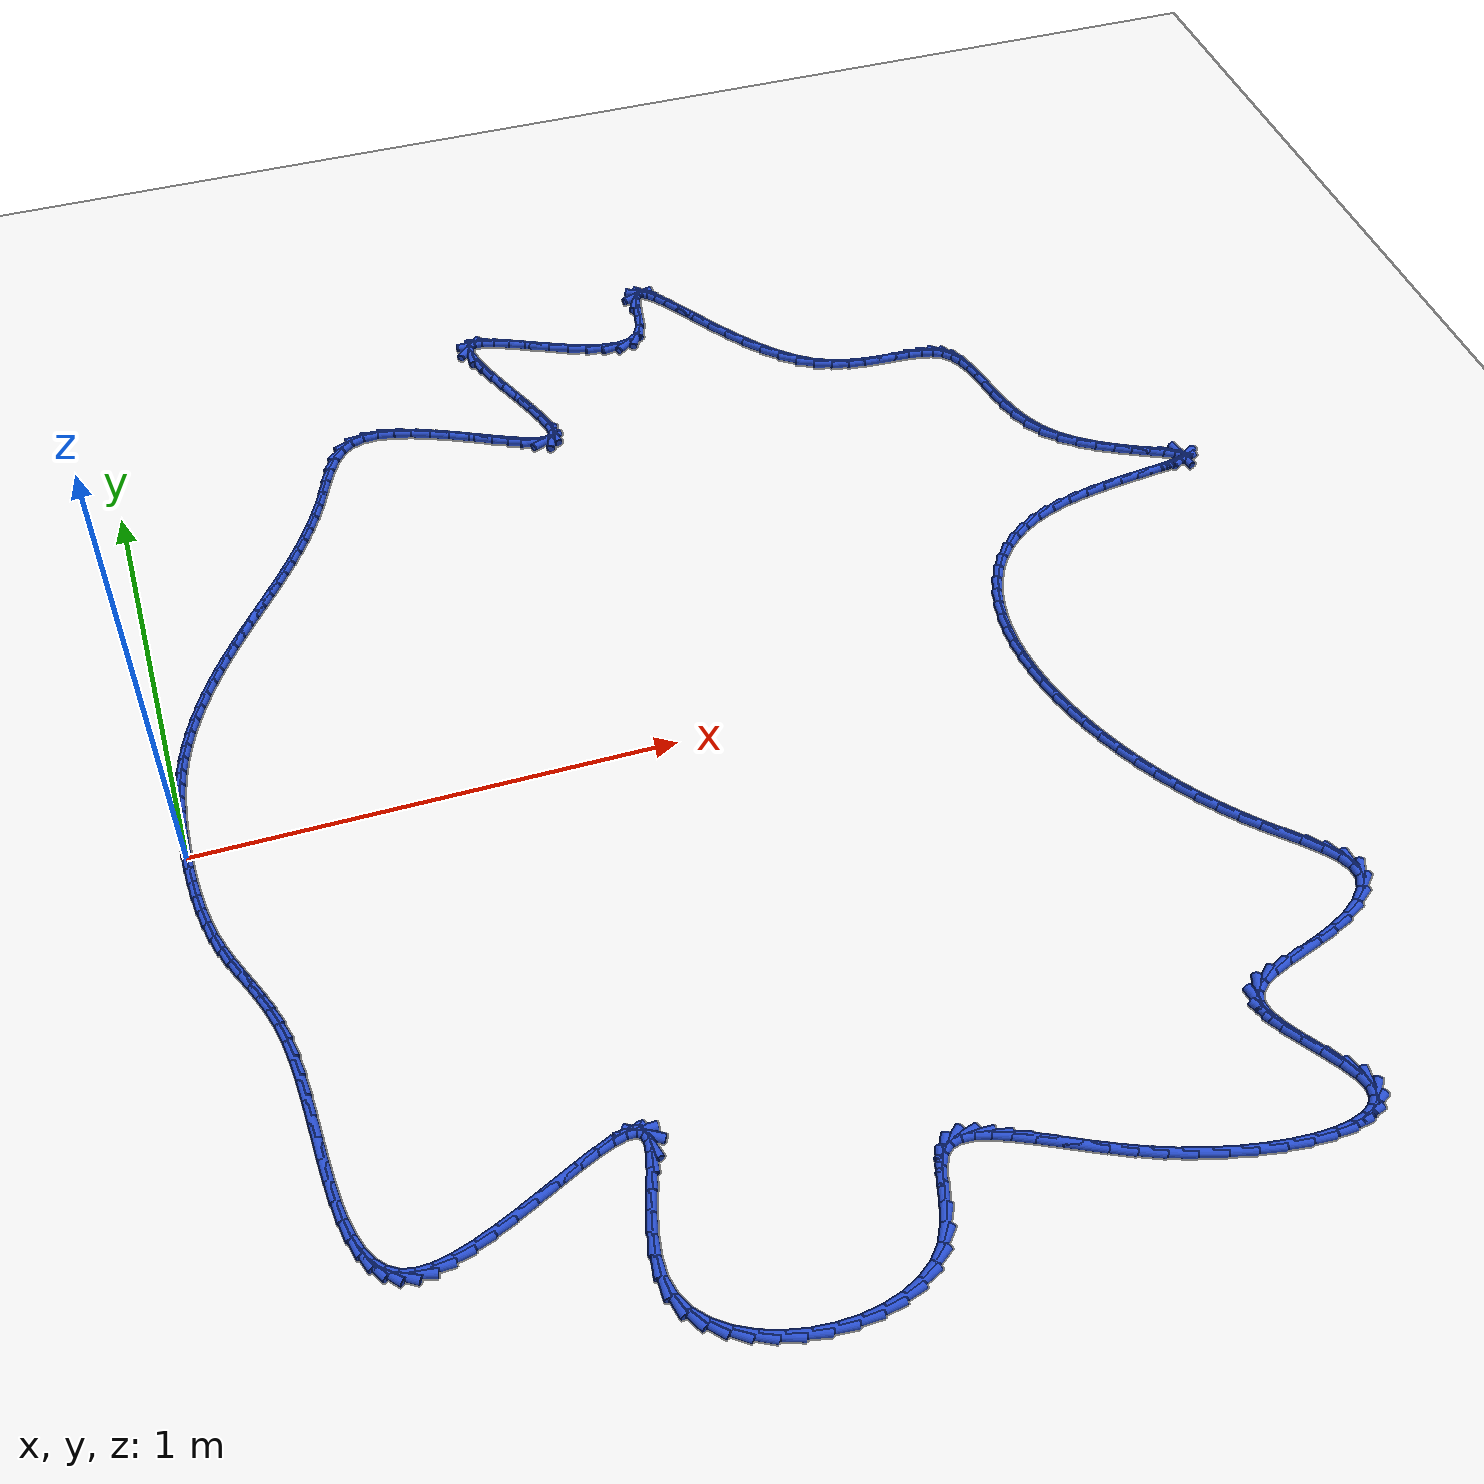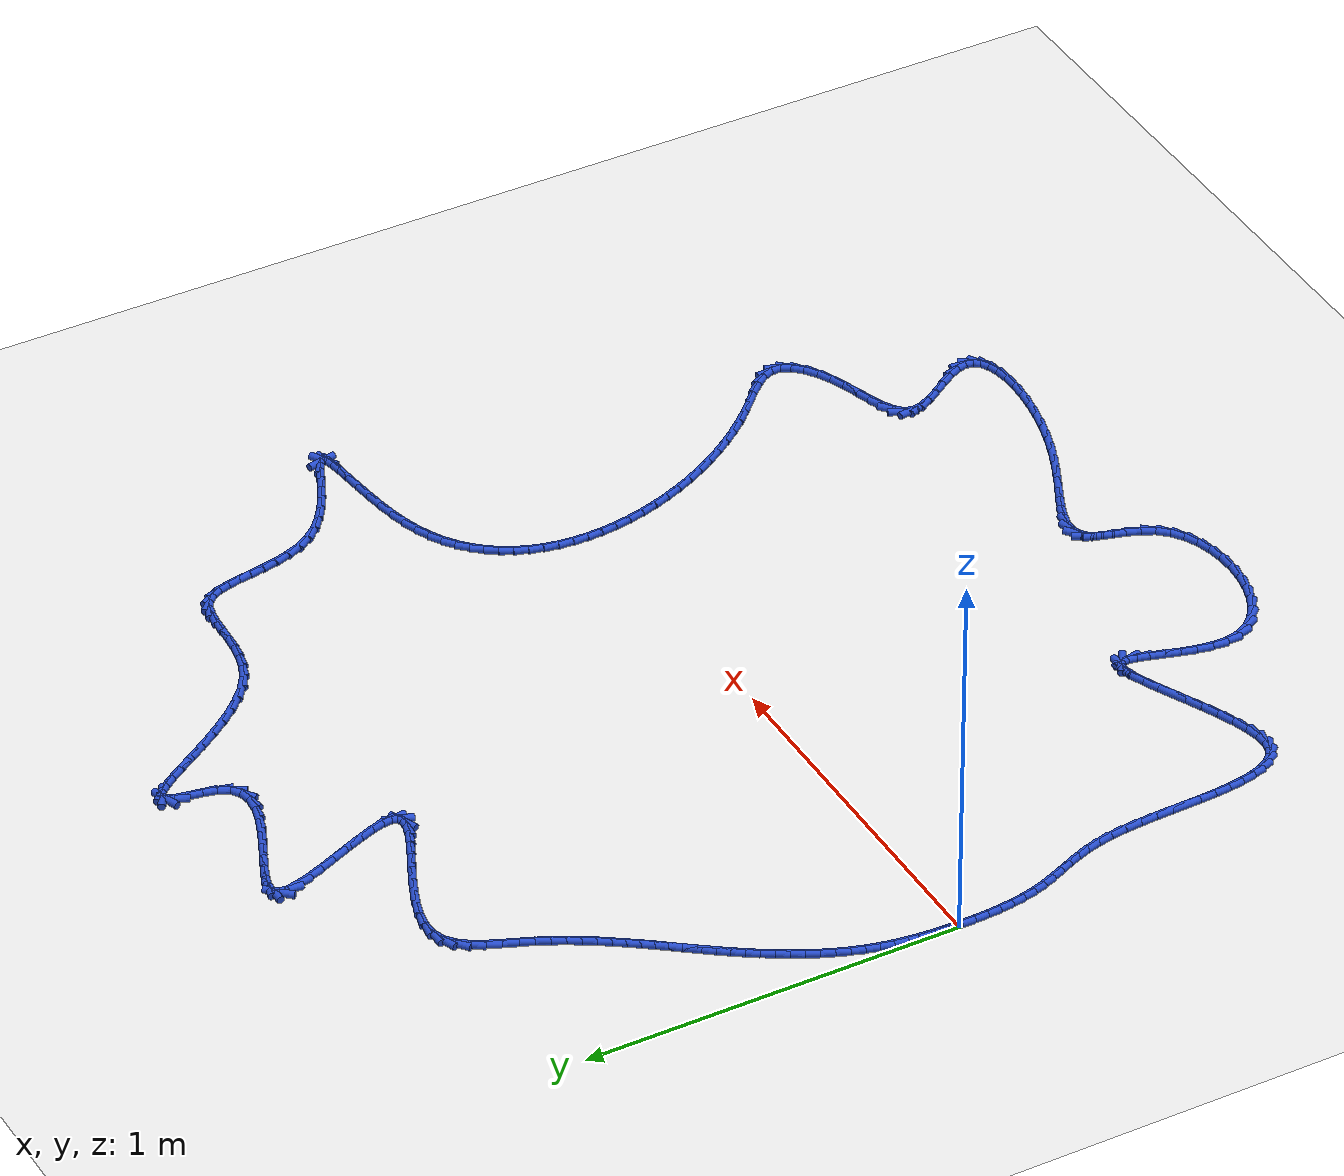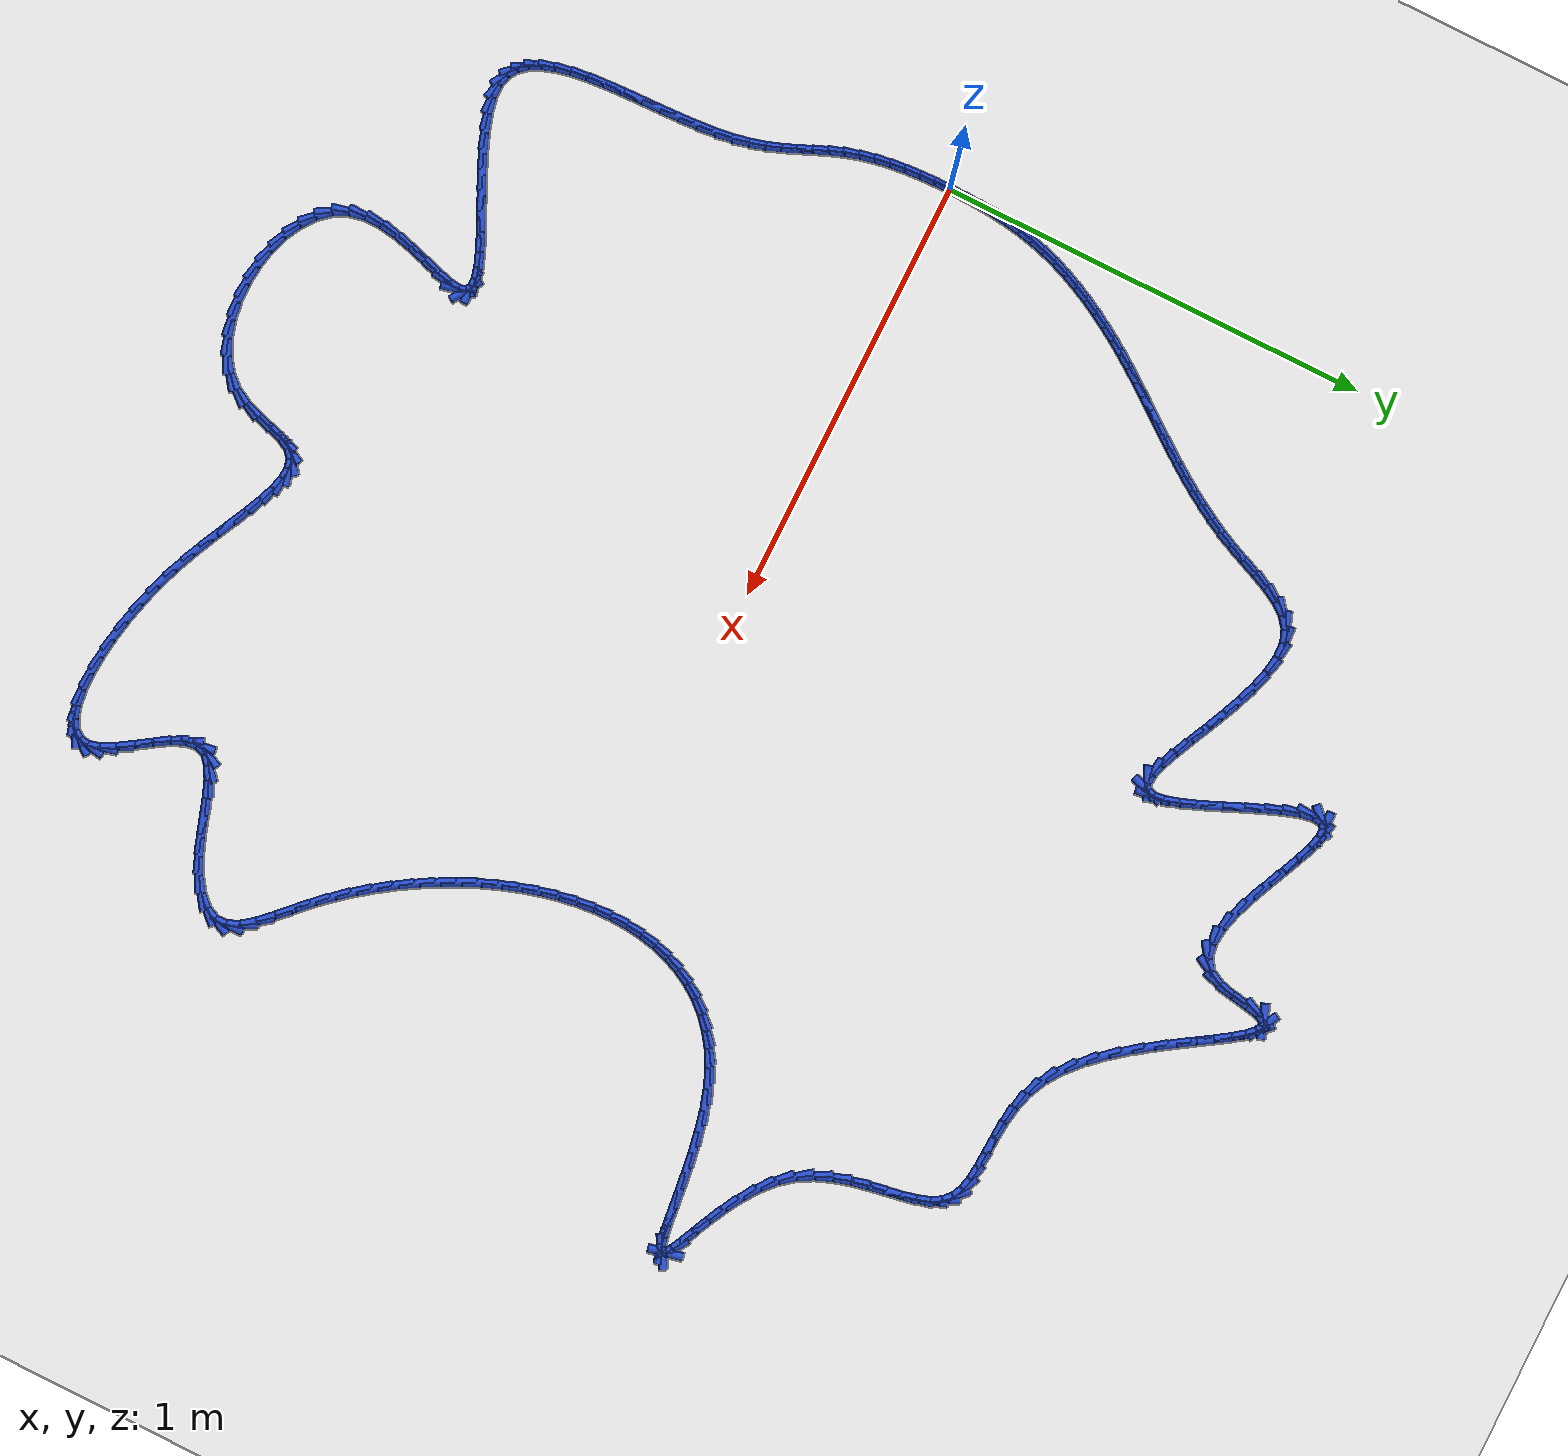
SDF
<sdf version="1.6">
 <world name="default">
  <light name="sun" type="directional">
   <pose>0 0 10 0 -0 0</pose>
   <diffuse>0.8 0.8 0.8 1</diffuse>
   <specular>0.2 0.2 0.2 1</specular>
   <attenuation>
    <range>1000</range>
    <constant>0.9</constant>
    <linear>0.01</linear>
    <quadratic>0.001</quadratic>
   </attenuation>
   <direction>-0.5 0.1 -0.9</direction>
  </light>
  <model name="ground_plane">
   <static>1</static>
   <link name="link">
    <collision name="collision">
     <geometry><plane><normal>0 0 1</normal><size>100 100</size></plane></geometry>
     <surface><friction><ode><mu>100</mu><mu2>50</mu2></ode></friction></surface>
    </collision>
    <visual name="visual">
     <cast_shadows>0</cast_shadows>
     <geometry><plane><normal>0 0 1</normal><size>100 100</size></plane></geometry>
     <material>
      <script><uri>file://media/materials/scripts/gazebo.material</uri><name>Gazebo/WhiteGlow</name></script>
     </material>
    </visual>
   </link>
  </model>
  <gravity>0 0 -9.8</gravity>
  <magnetic_field>6e-06 2.3e-05 -4.2e-05</magnetic_field>
  <atmosphere type="adiabatic"/>
  <physics name="default_physics" default="0" type="ode">
   <max_step_size>0.001</max_step_size>
   <real_time_factor>1</real_time_factor>
   <real_time_update_rate>1000</real_time_update_rate>
  </physics>
  <scene><ambient>0.4 0.4 0.4 1</ambient><background>0.7 0.7 0.7 1</background><shadows>1</shadows></scene>
  <spherical_coordinates>
   <surface_model>EARTH_WGS84</surface_model>
   <latitude_deg>0</latitude_deg>
   <longitude_deg>0</longitude_deg>
   <elevation>0</elevation>
   <heading_deg>0</heading_deg>
  </spherical_coordinates>
  <model name="line">
   <link name="link_0">
    <pose>1.3444106938820255e-17 -1.0408340855860843e-16 0.01 0 1.57 1.5540973294162868</pose>
    <collision name="collision">
     <geometry><cylinder><radius>0.01</radius><length>0.08</length></cylinder></geometry>
    </collision>
    <visual name="visual">
     <material>
      <script><name>Gazebo/Blue</name><uri>file://media/materials/scripts/gazebo.material</uri></script>
     </material>
     <geometry><cylinder><radius>0.01</radius><length>0.08</length></cylinder></geometry>
    </visual>
   </link>
   <link name="link_1">
    <pose>0.0005962556742878384 0.03570275726623297 0.01 0 1.57 1.5266809034565847</pose>
    <collision name="collision">
     <geometry><cylinder><radius>0.01</radius><length>0.08</length></cylinder></geometry>
    </collision>
    <visual name="visual">
     <material>
      <script><name>Gazebo/Blue</name><uri>file://media/materials/scripts/gazebo.material</uri></script>
     </material>
     <geometry><cylinder><radius>0.01</radius><length>0.08</length></cylinder></geometry>
    </visual>
   </link>
   <link name="link_2">
    <pose>0.0021618774195277524 0.071168946625515 0.01 0 1.57 1.4938641283382073</pose>
    <collision name="collision">
     <geometry><cylinder><radius>0.01</radius><length>0.08</length></cylinder></geometry>
    </collision>
    <visual name="visual">
     <material>
      <script><name>Gazebo/Blue</name><uri>file://media/materials/scripts/gazebo.material</uri></script>
     </material>
     <geometry><cylinder><radius>0.01</radius><length>0.08</length></cylinder></geometry>
    </visual>
   </link>
   <link name="link_3">
    <pose>0.00487525272768681 0.10636903390676378 0.01 0 1.57 1.455578202647358</pose>
    <collision name="collision">
     <geometry><cylinder><radius>0.01</radius><length>0.08</length></cylinder></geometry>
    </collision>
    <visual name="visual">
     <material>
      <script><name>Gazebo/Blue</name><uri>file://media/materials/scripts/gazebo.material</uri></script>
     </material>
     <geometry><cylinder><radius>0.01</radius><length>0.08</length></cylinder></geometry>
    </visual>
   </link>
   <link name="link_4">
    <pose>0.008914769090732067 0.14127348493889702 0.01 0 1.57 1.4118207604691668</pose>
    <collision name="collision">
     <geometry><cylinder><radius>0.01</radius><length>0.08</length></cylinder></geometry>
    </collision>
    <visual name="visual">
     <material>
      <script><name>Gazebo/Blue</name><uri>file://media/materials/scripts/gazebo.material</uri></script>
     </material>
     <geometry><cylinder><radius>0.01</radius><length>0.08</length></cylinder></geometry>
    </visual>
   </link>
   <link name="link_5">
    <pose>0.014458814000630576 0.17585276555083262 0.01 0 1.57 1.3626906049853438</pose>
    <collision name="collision">
     <geometry><cylinder><radius>0.01</radius><length>0.08</length></cylinder></geometry>
    </collision>
    <visual name="visual">
     <material>
      <script><name>Gazebo/Blue</name><uri>file://media/materials/scripts/gazebo.material</uri></script>
     </material>
     <geometry><cylinder><radius>0.01</radius><length>0.08</length></cylinder></geometry>
    </visual>
   </link>
   <link name="link_6">
    <pose>0.0216857749493494 0.21007734157148839 0.01 0 1.57 1.308523818144727</pose>
    <collision name="collision">
     <geometry><cylinder><radius>0.01</radius><length>0.08</length></cylinder></geometry>
    </collision>
    <visual name="visual">
     <material>
      <script><name>Gazebo/Blue</name><uri>file://media/materials/scripts/gazebo.material</uri></script>
     </material>
     <geometry><cylinder><radius>0.01</radius><length>0.08</length></cylinder></geometry>
    </visual>
   </link>
   <link name="link_7">
    <pose>0.030770375702281652 0.24391748311709124 0.01 0 1.57 1.2536198985429525</pose>
    <collision name="collision">
     <geometry><cylinder><radius>0.01</radius><length>0.08</length></cylinder></geometry>
    </collision>
    <visual name="visual">
     <material>
      <script><name>Gazebo/Blue</name><uri>file://media/materials/scripts/gazebo.material</uri></script>
     </material>
     <geometry><cylinder><radius>0.01</radius><length>0.08</length></cylinder></geometry>
    </visual>
   </link>
   <link name="link_8">
    <pose>0.04174016180733978 0.2773355981874211 0.01 0 1.57 1.2031949497875287</pose>
    <collision name="collision">
     <geometry><cylinder><radius>0.01</radius><length>0.08</length></cylinder></geometry>
    </collision>
    <visual name="visual">
     <material>
      <script><name>Gazebo/Blue</name><uri>file://media/materials/scripts/gazebo.material</uri></script>
     </material>
     <geometry><cylinder><radius>0.01</radius><length>0.08</length></cylinder></geometry>
    </visual>
   </link>
   <link name="link_9">
    <pose>0.054428694339304085 0.310283732321407 0.01 0 1.57 1.1573591260311897</pose>
    <collision name="collision">
     <geometry><cylinder><radius>0.01</radius><length>0.08</length></cylinder></geometry>
    </collision>
    <visual name="visual">
     <material>
      <script><name>Gazebo/Blue</name><uri>file://media/materials/scripts/gazebo.material</uri></script>
     </material>
     <geometry><cylinder><radius>0.01</radius><length>0.08</length></cylinder></geometry>
    </visual>
   </link>
   <link name="link_10">
    <pose>0.06865628506568291 0.34271322329294035 0.01 0 1.57 1.1158265058710326</pose>
    <collision name="collision">
     <geometry><cylinder><radius>0.01</radius><length>0.08</length></cylinder></geometry>
    </collision>
    <visual name="visual">
     <material>
      <script><name>Gazebo/Blue</name><uri>file://media/materials/scripts/gazebo.material</uri></script>
     </material>
     <geometry><cylinder><radius>0.01</radius><length>0.08</length></cylinder></geometry>
    </visual>
   </link>
   <link name="link_11">
    <pose>0.0842432457539847 0.37457540887591245 0.01 0 1.57 1.0783011402010652</pose>
    <collision name="collision">
     <geometry><cylinder><radius>0.01</radius><length>0.08</length></cylinder></geometry>
    </collision>
    <visual name="visual">
     <material>
      <script><name>Gazebo/Blue</name><uri>file://media/materials/scripts/gazebo.material</uri></script>
     </material>
     <geometry><cylinder><radius>0.01</radius><length>0.08</length></cylinder></geometry>
    </visual>
   </link>
   <link name="link_12">
    <pose>0.10100988817171773 0.4058216268442151 0.01 0 1.57 1.0444955488038663</pose>
    <collision name="collision">
     <geometry><cylinder><radius>0.01</radius><length>0.08</length></cylinder></geometry>
    </collision>
    <visual name="visual">
     <material>
      <script><name>Gazebo/Blue</name><uri>file://media/materials/scripts/gazebo.material</uri></script>
     </material>
     <geometry><cylinder><radius>0.01</radius><length>0.08</length></cylinder></geometry>
    </visual>
   </link>
   <link name="link_13">
    <pose>0.11877652408639047 0.43640321497173945 0.01 0 1.57 1.0141433413400252</pose>
    <collision name="collision">
     <geometry><cylinder><radius>0.01</radius><length>0.08</length></cylinder></geometry>
    </collision>
    <visual name="visual">
     <material>
      <script><name>Gazebo/Blue</name><uri>file://media/materials/scripts/gazebo.material</uri></script>
     </material>
     <geometry><cylinder><radius>0.01</radius><length>0.08</length></cylinder></geometry>
    </visual>
   </link>
   <link name="link_14">
    <pose>0.13736346526551124 0.4662715110323771 0.01 0 1.57 0.9870227367610622</pose>
    <collision name="collision">
     <geometry><cylinder><radius>0.01</radius><length>0.08</length></cylinder></geometry>
    </collision>
    <visual name="visual">
     <material>
      <script><name>Gazebo/Blue</name><uri>file://media/materials/scripts/gazebo.material</uri></script>
     </material>
     <geometry><cylinder><radius>0.01</radius><length>0.08</length></cylinder></geometry>
    </visual>
   </link>
   <link name="link_15">
    <pose>0.15659173019144332 0.4953798761029348 0.01 0 1.57 0.9636544328907303</pose>
    <collision name="collision">
     <geometry><cylinder><radius>0.01</radius><length>0.08</length></cylinder></geometry>
    </collision>
    <visual name="visual">
     <material>
      <script><name>Gazebo/Blue</name><uri>file://media/materials/scripts/gazebo.material</uri></script>
     </material>
     <geometry><cylinder><radius>0.01</radius><length>0.08</length></cylinder></geometry>
    </visual>
   </link>
   <link name="link_16">
    <pose>0.17631278960857188 0.5237688551507285 0.01 0 1.57 0.9451159483217858</pose>
    <collision name="collision">
     <geometry><cylinder><radius>0.01</radius><length>0.08</length></cylinder></geometry>
    </collision>
    <visual name="visual">
     <material>
      <script><name>Gazebo/Blue</name><uri>file://media/materials/scripts/gazebo.material</uri></script>
     </material>
     <geometry><cylinder><radius>0.01</radius><length>0.08</length></cylinder></geometry>
    </visual>
   </link>
   <link name="link_17">
    <pose>0.19641948788670976 0.5515974445614487 0.01 0 1.57 0.9317094310504189</pose>
    <collision name="collision">
     <geometry><cylinder><radius>0.01</radius><length>0.08</length></cylinder></geometry>
    </collision>
    <visual name="visual">
     <material>
      <script><name>Gazebo/Blue</name><uri>file://media/materials/scripts/gazebo.material</uri></script>
     </material>
     <geometry><cylinder><radius>0.01</radius><length>0.08</length></cylinder></geometry>
    </visual>
   </link>
   <link name="link_18">
    <pose>0.21680762490326466 0.5790331022482214 0.01 0 1.57 0.9235954429858738</pose>
    <collision name="collision">
     <geometry><cylinder><radius>0.01</radius><length>0.08</length></cylinder></geometry>
    </collision>
    <visual name="visual">
     <material>
      <script><name>Gazebo/Blue</name><uri>file://media/materials/scripts/gazebo.material</uri></script>
     </material>
     <geometry><cylinder><radius>0.01</radius><length>0.08</length></cylinder></geometry>
    </visual>
   </link>
   <link name="link_19">
    <pose>0.23737300053564445 0.6062432861241727 0.01 0 1.57 0.9208612967935044</pose>
    <collision name="collision">
     <geometry><cylinder><radius>0.01</radius><length>0.08</length></cylinder></geometry>
    </collision>
    <visual name="visual">
     <material>
      <script><name>Gazebo/Blue</name><uri>file://media/materials/scripts/gazebo.material</uri></script>
     </material>
     <geometry><cylinder><radius>0.01</radius><length>0.08</length></cylinder></geometry>
    </visual>
   </link>
   <link name="link_20">
    <pose>0.25801141466125677 0.6333954541024281 0.01 0 1.57 0.923525195483748</pose>
    <collision name="collision">
     <geometry><cylinder><radius>0.01</radius><length>0.08</length></cylinder></geometry>
    </collision>
    <visual name="visual">
     <material>
      <script><name>Gazebo/Blue</name><uri>file://media/materials/scripts/gazebo.material</uri></script>
     </material>
     <geometry><cylinder><radius>0.01</radius><length>0.08</length></cylinder></geometry>
    </visual>
   </link>
   <link name="link_21">
    <pose>0.27861866715750966 0.6606570640961146 0.01 0 1.57 0.9315381721507964</pose>
    <collision name="collision">
     <geometry><cylinder><radius>0.01</radius><length>0.08</length></cylinder></geometry>
    </collision>
    <visual name="visual">
     <material>
      <script><name>Gazebo/Blue</name><uri>file://media/materials/scripts/gazebo.material</uri></script>
     </material>
     <geometry><cylinder><radius>0.01</radius><length>0.08</length></cylinder></geometry>
    </visual>
   </link>
   <link name="link_22">
    <pose>0.29909055790181094 0.6881955740183578 0.01 0 1.57 0.9447835280982422</pose>
    <collision name="collision">
     <geometry><cylinder><radius>0.01</radius><length>0.08</length></cylinder></geometry>
    </collision>
    <visual name="visual">
     <material>
      <script><name>Gazebo/Blue</name><uri>file://media/materials/scripts/gazebo.material</uri></script>
     </material>
     <geometry><cylinder><radius>0.01</radius><length>0.08</length></cylinder></geometry>
    </visual>
   </link>
   <link name="link_23">
    <pose>0.3193228867715682 0.7161784417822838 0.01 0 1.57 0.963074153045013</pose>
    <collision name="collision">
     <geometry><cylinder><radius>0.01</radius><length>0.08</length></cylinder></geometry>
    </collision>
    <visual name="visual">
     <material>
      <script><name>Gazebo/Blue</name><uri>file://media/materials/scripts/gazebo.material</uri></script>
     </material>
     <geometry><cylinder><radius>0.01</radius><length>0.08</length></cylinder></geometry>
    </visual>
   </link>
   <link name="link_24">
    <pose>0.3392114536441894 0.7447731253010184 0.01 0 1.57 0.9861487482776489</pose>
    <collision name="collision">
     <geometry><cylinder><radius>0.01</radius><length>0.08</length></cylinder></geometry>
    </collision>
    <visual name="visual">
     <material>
      <script><name>Gazebo/Blue</name><uri>file://media/materials/scripts/gazebo.material</uri></script>
     </material>
     <geometry><cylinder><radius>0.01</radius><length>0.08</length></cylinder></geometry>
    </visual>
   </link>
   <link name="link_25">
    <pose>0.3586520583970824 0.7741470824876877 0.01 0 1.57 1.01366850116137</pose>
    <collision name="collision">
     <geometry><cylinder><radius>0.01</radius><length>0.08</length></cylinder></geometry>
    </collision>
    <visual name="visual">
     <material>
      <script><name>Gazebo/Blue</name><uri>file://media/materials/scripts/gazebo.material</uri></script>
     </material>
     <geometry><cylinder><radius>0.01</radius><length>0.08</length></cylinder></geometry>
    </visual>
   </link>
   <link name="link_26">
    <pose>0.3775405009076549 0.804467771255418 0.01 0 1.57 1.0452160859231854</pose>
    <collision name="collision">
     <geometry><cylinder><radius>0.01</radius><length>0.08</length></cylinder></geometry>
    </collision>
    <visual name="visual">
     <material>
      <script><name>Gazebo/Blue</name><uri>file://media/materials/scripts/gazebo.material</uri></script>
     </material>
     <geometry><cylinder><radius>0.01</radius><length>0.08</length></cylinder></geometry>
    </visual>
   </link>
   <link name="link_27">
    <pose>0.39577258105331475 0.8359026495173351 0.01 0 1.57 1.0802988757692995</pose>
    <collision name="collision">
     <geometry><cylinder><radius>0.01</radius><length>0.08</length></cylinder></geometry>
    </collision>
    <visual name="visual">
     <material>
      <script><name>Gazebo/Blue</name><uri>file://media/materials/scripts/gazebo.material</uri></script>
     </material>
     <geometry><cylinder><radius>0.01</radius><length>0.08</length></cylinder></geometry>
    </visual>
   </link>
   <link name="link_28">
    <pose>0.41324409871146967 0.8686191751865651 0.01 0 1.57 1.118357844758428</pose>
    <collision name="collision">
     <geometry><cylinder><radius>0.01</radius><length>0.08</length></cylinder></geometry>
    </collision>
    <visual name="visual">
     <material>
      <script><name>Gazebo/Blue</name><uri>file://media/materials/scripts/gazebo.material</uri></script>
     </material>
     <geometry><cylinder><radius>0.01</radius><length>0.08</length></cylinder></geometry>
    </visual>
   </link>
   <link name="link_29">
    <pose>0.4298508537595276 0.9027848061762339 0.01 0 1.57 1.1579581151346499</pose>
    <collision name="collision">
     <geometry><cylinder><radius>0.01</radius><length>0.08</length></cylinder></geometry>
    </collision>
    <visual name="visual">
     <material>
      <script><name>Gazebo/Blue</name><uri>file://media/materials/scripts/gazebo.material</uri></script>
     </material>
     <geometry><cylinder><radius>0.01</radius><length>0.08</length></cylinder></geometry>
    </visual>
   </link>
   <link name="link_30">
    <pose>0.4455087262615198 0.9385325783194586 0.01 0 1.57 1.176187809699897</pose>
    <collision name="collision">
     <geometry><cylinder><radius>0.01</radius><length>0.08</length></cylinder></geometry>
    </collision>
    <visual name="visual">
     <material>
      <script><name>Gazebo/Blue</name><uri>file://media/materials/scripts/gazebo.material</uri></script>
     </material>
     <geometry><cylinder><radius>0.01</radius><length>0.08</length></cylinder></geometry>
    </visual>
   </link>
   <link name="link_31">
    <pose>0.4607034467703435 0.9750186720301856 0.01 0 1.57 1.1485363390130836</pose>
    <collision name="collision">
     <geometry><cylinder><radius>0.01</radius><length>0.08</length></cylinder></geometry>
    </collision>
    <visual name="visual">
     <material>
      <script><name>Gazebo/Blue</name><uri>file://media/materials/scripts/gazebo.material</uri></script>
     </material>
     <geometry><cylinder><radius>0.01</radius><length>0.08</length></cylinder></geometry>
    </visual>
   </link>
   <link name="link_32">
    <pose>0.47655796494757274 1.0103069269212723 0.01 0 1.57 1.0675294267235134</pose>
    <collision name="collision">
     <geometry><cylinder><radius>0.01</radius><length>0.08</length></cylinder></geometry>
    </collision>
    <visual name="visual">
     <material>
      <script><name>Gazebo/Blue</name><uri>file://media/materials/scripts/gazebo.material</uri></script>
     </material>
     <geometry><cylinder><radius>0.01</radius><length>0.08</length></cylinder></geometry>
    </visual>
   </link>
   <link name="link_33">
    <pose>0.4942288371236857 1.0424035730092327 0.01 0 1.57 0.9164372473508</pose>
    <collision name="collision">
     <geometry><cylinder><radius>0.01</radius><length>0.08</length></cylinder></geometry>
    </collision>
    <visual name="visual">
     <material>
      <script><name>Gazebo/Blue</name><uri>file://media/materials/scripts/gazebo.material</uri></script>
     </material>
     <geometry><cylinder><radius>0.01</radius><length>0.08</length></cylinder></geometry>
    </visual>
   </link>
   <link name="link_34">
    <pose>0.5148726196291603 1.069314840310581 0.01 0 1.57 0.6726087202908481</pose>
    <collision name="collision">
     <geometry><cylinder><radius>0.01</radius><length>0.08</length></cylinder></geometry>
    </collision>
    <visual name="visual">
     <material>
      <script><name>Gazebo/Blue</name><uri>file://media/materials/scripts/gazebo.material</uri></script>
     </material>
     <geometry><cylinder><radius>0.01</radius><length>0.08</length></cylinder></geometry>
    </visual>
   </link>
   <link name="link_35">
    <pose>0.5396458687944746 1.089046958841831 0.01 0 1.57 0.3423638444105744</pose>
    <collision name="collision">
     <geometry><cylinder><radius>0.01</radius><length>0.08</length></cylinder></geometry>
    </collision>
    <visual name="visual">
     <material>
      <script><name>Gazebo/Blue</name><uri>file://media/materials/scripts/gazebo.material</uri></script>
     </material>
     <geometry><cylinder><radius>0.01</radius><length>0.08</length></cylinder></geometry>
    </visual>
   </link>
   <link name="link_36">
    <pose>0.5696240729774585 1.0997311530559803 0.01 0 1.57 0.047931330549219525</pose>
    <collision name="collision">
     <geometry><cylinder><radius>0.01</radius><length>0.08</length></cylinder></geometry>
    </collision>
    <visual name="visual">
     <material>
      <script><name>Gazebo/Blue</name><uri>file://media/materials/scripts/gazebo.material</uri></script>
     </material>
     <geometry><cylinder><radius>0.01</radius><length>0.08</length></cylinder></geometry>
    </visual>
   </link>
   <link name="link_37">
    <pose>0.6046424740166854 1.1014109181796632 0.01 0 1.57 -0.14759777339000985</pose>
    <collision name="collision">
     <geometry><cylinder><radius>0.01</radius><length>0.08</length></cylinder></geometry>
    </collision>
    <visual name="visual">
     <material>
      <script><name>Gazebo/Blue</name><uri>file://media/materials/scripts/gazebo.material</uri></script>
     </material>
     <geometry><cylinder><radius>0.01</radius><length>0.08</length></cylinder></geometry>
    </visual>
   </link>
   <link name="link_38">
    <pose>0.6435674485802125 1.0956235916075074 0.01 0 1.57 -0.2732126726696202</pose>
    <collision name="collision">
     <geometry><cylinder><radius>0.01</radius><length>0.08</length></cylinder></geometry>
    </collision>
    <visual name="visual">
     <material>
      <script><name>Gazebo/Blue</name><uri>file://media/materials/scripts/gazebo.material</uri></script>
     </material>
     <geometry><cylinder><radius>0.01</radius><length>0.08</length></cylinder></geometry>
    </visual>
   </link>
   <link name="link_39">
    <pose>0.6852396212715328 1.0839462164859146 0.01 0 1.57 -0.3540582654534181</pose>
    <collision name="collision">
     <geometry><cylinder><radius>0.01</radius><length>0.08</length></cylinder></geometry>
    </collision>
    <visual name="visual">
     <material>
      <script><name>Gazebo/Blue</name><uri>file://media/materials/scripts/gazebo.material</uri></script>
     </material>
     <geometry><cylinder><radius>0.01</radius><length>0.08</length></cylinder></geometry>
    </visual>
   </link>
   <link name="link_40">
    <pose>0.7284996166941375 1.067955835961284 0.01 0 1.57 -0.4049444694214107</pose>
    <collision name="collision">
     <geometry><cylinder><radius>0.01</radius><length>0.08</length></cylinder></geometry>
    </collision>
    <visual name="visual">
     <material>
      <script><name>Gazebo/Blue</name><uri>file://media/materials/scripts/gazebo.material</uri></script>
     </material>
     <geometry><cylinder><radius>0.01</radius><length>0.08</length></cylinder></geometry>
    </visual>
   </link>
   <link name="link_41">
    <pose>0.7721880594515192 1.0492294931800166 0.01 0 1.57 -0.4335340104082877</pose>
    <collision name="collision">
     <geometry><cylinder><radius>0.01</radius><length>0.08</length></cylinder></geometry>
    </collision>
    <visual name="visual">
     <material>
      <script><name>Gazebo/Blue</name><uri>file://media/materials/scripts/gazebo.material</uri></script>
     </material>
     <geometry><cylinder><radius>0.01</radius><length>0.08</length></cylinder></geometry>
    </visual>
   </link>
   <link name="link_42">
    <pose>0.8151455741471703 1.0293442312885126 0.01 0 1.57 -0.44265755465520296</pose>
    <collision name="collision">
     <geometry><cylinder><radius>0.01</radius><length>0.08</length></cylinder></geometry>
    </collision>
    <visual name="visual">
     <material>
      <script><name>Gazebo/Blue</name><uri>file://media/materials/scripts/gazebo.material</uri></script>
     </material>
     <geometry><cylinder><radius>0.01</radius><length>0.08</length></cylinder></geometry>
    </visual>
   </link>
   <link name="link_43">
    <pose>0.8562127853845827 1.0098770934331733 0.01 0 1.57 -0.4307892814029892</pose>
    <collision name="collision">
     <geometry><cylinder><radius>0.01</radius><length>0.08</length></cylinder></geometry>
    </collision>
    <visual name="visual">
     <material>
      <script><name>Gazebo/Blue</name><uri>file://media/materials/scripts/gazebo.material</uri></script>
     </material>
     <geometry><cylinder><radius>0.01</radius><length>0.08</length></cylinder></geometry>
    </visual>
   </link>
   <link name="link_44">
    <pose>0.8942303177672484 0.9924051227603986 0.01 0 1.57 -0.3900662727399321</pose>
    <collision name="collision">
     <geometry><cylinder><radius>0.01</radius><length>0.08</length></cylinder></geometry>
    </collision>
    <visual name="visual">
     <material>
      <script><name>Gazebo/Blue</name><uri>file://media/materials/scripts/gazebo.material</uri></script>
     </material>
     <geometry><cylinder><radius>0.01</radius><length>0.08</length></cylinder></geometry>
    </visual>
   </link>
   <link name="link_45">
    <pose>0.9280387958986593 0.9785053624165888 0.01 0 1.57 -0.29849002512948114</pose>
    <collision name="collision">
     <geometry><cylinder><radius>0.01</radius><length>0.08</length></cylinder></geometry>
    </collision>
    <visual name="visual">
     <material>
      <script><name>Gazebo/Blue</name><uri>file://media/materials/scripts/gazebo.material</uri></script>
     </material>
     <geometry><cylinder><radius>0.01</radius><length>0.08</length></cylinder></geometry>
    </visual>
   </link>
   <link name="link_46">
    <pose>0.9564788443823079 0.9697548555481451 0.01 0 1.57 -0.09211660835350824</pose>
    <collision name="collision">
     <geometry><cylinder><radius>0.01</radius><length>0.08</length></cylinder></geometry>
    </collision>
    <visual name="visual">
     <material>
      <script><name>Gazebo/Blue</name><uri>file://media/materials/scripts/gazebo.material</uri></script>
     </material>
     <geometry><cylinder><radius>0.01</radius><length>0.08</length></cylinder></geometry>
    </visual>
   </link>
   <link name="link_47">
    <pose>0.9783910878216858 0.9677306453014669 0.01 0 1.57 0.41569017660578866</pose>
    <collision name="collision">
     <geometry><cylinder><radius>0.01</radius><length>0.08</length></cylinder></geometry>
    </collision>
    <visual name="visual">
     <material>
      <script><name>Gazebo/Blue</name><uri>file://media/materials/scripts/gazebo.material</uri></script>
     </material>
     <geometry><cylinder><radius>0.01</radius><length>0.08</length></cylinder></geometry>
    </visual>
   </link>
   <link name="link_48">
    <pose>0.9926161508202862 0.9740097748229557 0.01 0 1.57 1.2441062371827094</pose>
    <collision name="collision">
     <geometry><cylinder><radius>0.01</radius><length>0.08</length></cylinder></geometry>
    </collision>
    <visual name="visual">
     <material>
      <script><name>Gazebo/Blue</name><uri>file://media/materials/scripts/gazebo.material</uri></script>
     </material>
     <geometry><cylinder><radius>0.01</radius><length>0.08</length></cylinder></geometry>
    </visual>
   </link>
   <link name="link_49">
    <pose>0.998063309506109 0.990086113370722 0.01 0 1.57 -1.4553379725789222</pose>
    <collision name="collision">
     <geometry><cylinder><radius>0.01</radius><length>0.08</length></cylinder></geometry>
    </collision>
    <visual name="visual">
     <material>
      <script><name>Gazebo/Blue</name><uri>file://media/materials/scripts/gazebo.material</uri></script>
     </material>
     <geometry><cylinder><radius>0.01</radius><length>0.08</length></cylinder></geometry>
    </visual>
   </link>
   <link name="link_50">
    <pose>0.9950933429816454 1.015694980088876 0.01 0 1.57 -1.2881413071022747</pose>
    <collision name="collision">
     <geometry><cylinder><radius>0.01</radius><length>0.08</length></cylinder></geometry>
    </collision>
    <visual name="visual">
     <material>
      <script><name>Gazebo/Blue</name><uri>file://media/materials/scripts/gazebo.material</uri></script>
     </material>
     <geometry><cylinder><radius>0.01</radius><length>0.08</length></cylinder></geometry>
    </visual>
   </link>
   <link name="link_51">
    <pose>0.9854510553352902 1.048894896113171 0.01 0 1.57 -1.212677871284093</pose>
    <collision name="collision">
     <geometry><cylinder><radius>0.01</radius><length>0.08</length></cylinder></geometry>
    </collision>
    <visual name="visual">
     <material>
      <script><name>Gazebo/Blue</name><uri>file://media/materials/scripts/gazebo.material</uri></script>
     </material>
     <geometry><cylinder><radius>0.01</radius><length>0.08</length></cylinder></geometry>
    </visual>
   </link>
   <link name="link_52">
    <pose>0.9709363969944836 1.0876775707281172 0.01 0 1.57 -1.1772476468073936</pose>
    <collision name="collision">
     <geometry><cylinder><radius>0.01</radius><length>0.08</length></cylinder></geometry>
    </collision>
    <visual name="visual">
     <material>
      <script><name>Gazebo/Blue</name><uri>file://media/materials/scripts/gazebo.material</uri></script>
     </material>
     <geometry><cylinder><radius>0.01</radius><length>0.08</length></cylinder></geometry>
    </visual>
   </link>
   <link name="link_53">
    <pose>0.9533493183866659 1.1300347132182236 0.01 0 1.57 -1.1652263763859736</pose>
    <collision name="collision">
     <geometry><cylinder><radius>0.01</radius><length>0.08</length></cylinder></geometry>
    </collision>
    <visual name="visual">
     <material>
      <script><name>Gazebo/Blue</name><uri>file://media/materials/scripts/gazebo.material</uri></script>
     </material>
     <geometry><cylinder><radius>0.01</radius><length>0.08</length></cylinder></geometry>
    </visual>
   </link>
   <link name="link_54">
    <pose>0.9344897699392769 1.1739580328679984 0.01 0 1.57 -1.1718013885289402</pose>
    <collision name="collision">
     <geometry><cylinder><radius>0.01</radius><length>0.08</length></cylinder></geometry>
    </collision>
    <visual name="visual">
     <material>
      <script><name>Gazebo/Blue</name><uri>file://media/materials/scripts/gazebo.material</uri></script>
     </material>
     <geometry><cylinder><radius>0.01</radius><length>0.08</length></cylinder></geometry>
    </visual>
   </link>
   <link name="link_55">
    <pose>0.916157702079757 1.2174392389619513 0.01 0 1.57 -1.1988847422950504</pose>
    <collision name="collision">
     <geometry><cylinder><radius>0.01</radius><length>0.08</length></cylinder></geometry>
    </collision>
    <visual name="visual">
     <material>
      <script><name>Gazebo/Blue</name><uri>file://media/materials/scripts/gazebo.material</uri></script>
     </material>
     <geometry><cylinder><radius>0.01</radius><length>0.08</length></cylinder></geometry>
    </visual>
   </link>
   <link name="link_56">
    <pose>0.9001530652355461 1.258470040784591 0.01 0 1.57 -1.2567790911932688</pose>
    <collision name="collision">
     <geometry><cylinder><radius>0.01</radius><length>0.08</length></cylinder></geometry>
    </collision>
    <visual name="visual">
     <material>
      <script><name>Gazebo/Blue</name><uri>file://media/materials/scripts/gazebo.material</uri></script>
     </material>
     <geometry><cylinder><radius>0.01</radius><length>0.08</length></cylinder></geometry>
    </visual>
   </link>
   <link name="link_57">
    <pose>0.8882758098340845 1.2950421476204261 0.01 0 1.57 -1.3756727059972798</pose>
    <collision name="collision">
     <geometry><cylinder><radius>0.01</radius><length>0.08</length></cylinder></geometry>
    </collision>
    <visual name="visual">
     <material>
      <script><name>Gazebo/Blue</name><uri>file://media/materials/scripts/gazebo.material</uri></script>
     </material>
     <geometry><cylinder><radius>0.01</radius><length>0.08</length></cylinder></geometry>
    </visual>
   </link>
   <link name="link_58">
    <pose>0.8823258863028123 1.3251472687539665 0.01 0 1.57 1.488808935050676</pose>
    <collision name="collision">
     <geometry><cylinder><radius>0.01</radius><length>0.08</length></cylinder></geometry>
    </collision>
    <visual name="visual">
     <material>
      <script><name>Gazebo/Blue</name><uri>file://media/materials/scripts/gazebo.material</uri></script>
     </material>
     <geometry><cylinder><radius>0.01</radius><length>0.08</length></cylinder></geometry>
    </visual>
   </link>
   <link name="link_59">
    <pose>0.8841032450691694 1.3467771134697204 0.01 0 1.57 0.783674373571665</pose>
    <collision name="collision">
     <geometry><cylinder><radius>0.01</radius><length>0.08</length></cylinder></geometry>
    </collision>
    <visual name="visual">
     <material>
      <script><name>Gazebo/Blue</name><uri>file://media/materials/scripts/gazebo.material</uri></script>
     </material>
     <geometry><cylinder><radius>0.01</radius><length>0.08</length></cylinder></geometry>
    </visual>
   </link>
   <link name="link_60">
    <pose>0.8953536329190005 1.3579887814179492 0.01 0 1.57 0.03589237560926918</pose>
    <collision name="collision">
     <geometry><cylinder><radius>0.01</radius><length>0.08</length></cylinder></geometry>
    </collision>
    <visual name="visual">
     <material>
      <script><name>Gazebo/Blue</name><uri>file://media/materials/scripts/gazebo.material</uri></script>
     </material>
     <geometry><cylinder><radius>0.01</radius><length>0.08</length></cylinder></geometry>
    </visual>
   </link>
   <link name="link_61">
    <pose>0.9162481033970835 1.3587390558116663 0.01 0 1.57 -0.2570705202658405</pose>
    <collision name="collision">
     <geometry><cylinder><radius>0.01</radius><length>0.08</length></cylinder></geometry>
    </collision>
    <visual name="visual">
     <material>
      <script><name>Gazebo/Blue</name><uri>file://media/materials/scripts/gazebo.material</uri></script>
     </material>
     <geometry><cylinder><radius>0.01</radius><length>0.08</length></cylinder></geometry>
    </visual>
   </link>
   <link name="link_62">
    <pose>0.9451758542617804 1.3511343208530635 0.01 0 1.57 -0.37157371935572914</pose>
    <collision name="collision">
     <geometry><cylinder><radius>0.01</radius><length>0.08</length></cylinder></geometry>
    </collision>
    <visual name="visual">
     <material>
      <script><name>Gazebo/Blue</name><uri>file://media/materials/scripts/gazebo.material</uri></script>
     </material>
     <geometry><cylinder><radius>0.01</radius><length>0.08</length></cylinder></geometry>
    </visual>
   </link>
   <link name="link_63">
    <pose>0.9804302486156251 1.3373965740686726 0.01 0 1.57 -0.41669043497743213</pose>
    <collision name="collision">
     <geometry><cylinder><radius>0.01</radius><length>0.08</length></cylinder></geometry>
    </collision>
    <visual name="visual">
     <material>
      <script><name>Gazebo/Blue</name><uri>file://media/materials/scripts/gazebo.material</uri></script>
     </material>
     <geometry><cylinder><radius>0.01</radius><length>0.08</length></cylinder></geometry>
    </visual>
   </link>
   <link name="link_64">
    <pose>1.0203046495611527 1.3197478129850277 0.01 0 1.57 -0.424471354114581</pose>
    <collision name="collision">
     <geometry><cylinder><radius>0.01</radius><length>0.08</length></cylinder></geometry>
    </collision>
    <visual name="visual">
     <material>
      <script><name>Gazebo/Blue</name><uri>file://media/materials/scripts/gazebo.material</uri></script>
     </material>
     <geometry><cylinder><radius>0.01</radius><length>0.08</length></cylinder></geometry>
    </visual>
   </link>
   <link name="link_65">
    <pose>1.0630924202008973 1.3004100351286614 0.01 0 1.57 -0.40393143059395986</pose>
    <collision name="collision">
     <geometry><cylinder><radius>0.01</radius><length>0.08</length></cylinder></geometry>
    </collision>
    <visual name="visual">
     <material>
      <script><name>Gazebo/Blue</name><uri>file://media/materials/scripts/gazebo.material</uri></script>
     </material>
     <geometry><cylinder><radius>0.01</radius><length>0.08</length></cylinder></geometry>
    </visual>
   </link>
   <link name="link_66">
    <pose>1.1070869236373935 1.2816052380261067 0.01 0 1.57 -0.35350635505028494</pose>
    <collision name="collision">
     <geometry><cylinder><radius>0.01</radius><length>0.08</length></cylinder></geometry>
    </collision>
    <visual name="visual">
     <material>
      <script><name>Gazebo/Blue</name><uri>file://media/materials/scripts/gazebo.material</uri></script>
     </material>
     <geometry><cylinder><radius>0.01</radius><length>0.08</length></cylinder></geometry>
    </visual>
   </link>
   <link name="link_67">
    <pose>1.1505815229731746 1.2655554192038965 0.01 0 1.57 -0.2620195012930942</pose>
    <collision name="collision">
     <geometry><cylinder><radius>0.01</radius><length>0.08</length></cylinder></geometry>
    </collision>
    <visual name="visual">
     <material>
      <script><name>Gazebo/Blue</name><uri>file://media/materials/scripts/gazebo.material</uri></script>
     </material>
     <geometry><cylinder><radius>0.01</radius><length>0.08</length></cylinder></geometry>
    </visual>
   </link>
   <link name="link_68">
    <pose>1.1918695813107774 1.254482576188563 0.01 0 1.57 -0.10328022176700588</pose>
    <collision name="collision">
     <geometry><cylinder><radius>0.01</radius><length>0.08</length></cylinder></geometry>
    </collision>
    <visual name="visual">
     <material>
      <script><name>Gazebo/Blue</name><uri>file://media/materials/scripts/gazebo.material</uri></script>
     </material>
     <geometry><cylinder><radius>0.01</radius><length>0.08</length></cylinder></geometry>
    </visual>
   </link>
   <link name="link_69">
    <pose>1.2292444617527345 1.2506087065066405 0.01 0 1.57 0.17293901825273011</pose>
    <collision name="collision">
     <geometry><cylinder><radius>0.01</radius><length>0.08</length></cylinder></geometry>
    </collision>
    <visual name="visual">
     <material>
      <script><name>Gazebo/Blue</name><uri>file://media/materials/scripts/gazebo.material</uri></script>
     </material>
     <geometry><cylinder><radius>0.01</radius><length>0.08</length></cylinder></geometry>
    </visual>
   </link>
   <link name="link_70">
    <pose>1.2609995274015797 1.2561558076846602 0.01 0 1.57 0.6131953967773918</pose>
    <collision name="collision">
     <geometry><cylinder><radius>0.01</radius><length>0.08</length></cylinder></geometry>
    </collision>
    <visual name="visual">
     <material>
      <script><name>Gazebo/Blue</name><uri>file://media/materials/scripts/gazebo.material</uri></script>
     </material>
     <geometry><cylinder><radius>0.01</radius><length>0.08</length></cylinder></geometry>
    </visual>
   </link>
   <link name="link_71">
    <pose>1.2854281413598494 1.2733458772491562 0.01 0 1.57 1.0797481965567843</pose>
    <collision name="collision">
     <geometry><cylinder><radius>0.01</radius><length>0.08</length></cylinder></geometry>
    </collision>
    <visual name="visual">
     <material>
      <script><name>Gazebo/Blue</name><uri>file://media/materials/scripts/gazebo.material</uri></script>
     </material>
     <geometry><cylinder><radius>0.01</radius><length>0.08</length></cylinder></geometry>
    </visual>
   </link>
   <link name="link_72">
    <pose>1.3014098006461987 1.3032329288068003 0.01 0 1.57 1.3195860041165246</pose>
    <collision name="collision">
     <geometry><cylinder><radius>0.01</radius><length>0.08</length></cylinder></geometry>
    </collision>
    <visual name="visual">
     <material>
      <script><name>Gazebo/Blue</name><uri>file://media/materials/scripts/gazebo.material</uri></script>
     </material>
     <geometry><cylinder><radius>0.01</radius><length>0.08</length></cylinder></geometry>
    </visual>
   </link>
   <link name="link_73">
    <pose>1.3109897678020552 1.3405625827405399 0.01 0 1.57 1.4042285050539571</pose>
    <collision name="collision">
     <geometry><cylinder><radius>0.01</radius><length>0.08</length></cylinder></geometry>
    </collision>
    <visual name="visual">
     <material>
      <script><name>Gazebo/Blue</name><uri>file://media/materials/scripts/gazebo.material</uri></script>
     </material>
     <geometry><cylinder><radius>0.01</radius><length>0.08</length></cylinder></geometry>
    </visual>
   </link>
   <link name="link_74">
    <pose>1.3172772787663003 1.3779602889651004 0.01 0 1.57 1.3706171806686047</pose>
    <collision name="collision">
     <geometry><cylinder><radius>0.01</radius><length>0.08</length></cylinder></geometry>
    </collision>
    <visual name="visual">
     <material>
      <script><name>Gazebo/Blue</name><uri>file://media/materials/scripts/gazebo.material</uri></script>
     </material>
     <geometry><cylinder><radius>0.01</radius><length>0.08</length></cylinder></geometry>
    </visual>
   </link>
   <link name="link_75">
    <pose>1.3233823610823776 1.4080499199768746 0.01 0 1.57 1.1054465272666518</pose>
    <collision name="collision">
     <geometry><cylinder><radius>0.01</radius><length>0.08</length></cylinder></geometry>
    </collision>
    <visual name="visual">
     <material>
      <script><name>Gazebo/Blue</name><uri>file://media/materials/scripts/gazebo.material</uri></script>
     </material>
     <geometry><cylinder><radius>0.01</radius><length>0.08</length></cylinder></geometry>
    </visual>
   </link>
   <link name="link_76">
    <pose>1.331876730161807 1.424966608178737 0.01 0 1.57 0.33051205854369414</pose>
    <collision name="collision">
     <geometry><cylinder><radius>0.01</radius><length>0.08</length></cylinder></geometry>
    </collision>
    <visual name="visual">
     <material>
      <script><name>Gazebo/Blue</name><uri>file://media/materials/scripts/gazebo.material</uri></script>
     </material>
     <geometry><cylinder><radius>0.01</radius><length>0.08</length></cylinder></geometry>
    </visual>
   </link>
   <link name="link_77">
    <pose>1.3431935146351943 1.4288493641454747 0.01 0 1.57 -0.4917693095500789</pose>
    <collision name="collision">
     <geometry><cylinder><radius>0.01</radius><length>0.08</length></cylinder></geometry>
    </collision>
    <visual name="visual">
     <material>
      <script><name>Gazebo/Blue</name><uri>file://media/materials/scripts/gazebo.material</uri></script>
     </material>
     <geometry><cylinder><radius>0.01</radius><length>0.08</length></cylinder></geometry>
    </visual>
   </link>
   <link name="link_78">
    <pose>1.3572348369504987 1.4213279476034106 0.01 0 1.57 -0.8038818135464397</pose>
    <collision name="collision">
     <geometry><cylinder><radius>0.01</radius><length>0.08</length></cylinder></geometry>
    </collision>
    <visual name="visual">
     <material>
      <script><name>Gazebo/Blue</name><uri>file://media/materials/scripts/gazebo.material</uri></script>
     </material>
     <geometry><cylinder><radius>0.01</radius><length>0.08</length></cylinder></geometry>
    </visual>
   </link>
   <link name="link_79">
    <pose>1.37390281955568 1.4040321182788673 0.01 0 1.57 -0.9243733077283942</pose>
    <collision name="collision">
     <geometry><cylinder><radius>0.01</radius><length>0.08</length></cylinder></geometry>
    </collision>
    <visual name="visual">
     <material>
      <script><name>Gazebo/Blue</name><uri>file://media/materials/scripts/gazebo.material</uri></script>
     </material>
     <geometry><cylinder><radius>0.01</radius><length>0.08</length></cylinder></geometry>
    </visual>
   </link>
   <link name="link_80">
    <pose>1.393099584898697 1.3785916358981682 0.01 0 1.57 -0.9758052666844227</pose>
    <collision name="collision">
     <geometry><cylinder><radius>0.01</radius><length>0.08</length></cylinder></geometry>
    </collision>
    <visual name="visual">
     <material>
      <script><name>Gazebo/Blue</name><uri>file://media/materials/scripts/gazebo.material</uri></script>
     </material>
     <geometry><cylinder><radius>0.01</radius><length>0.08</length></cylinder></geometry>
    </visual>
   </link>
   <link name="link_81">
    <pose>1.4147272554275112 1.3466362601876354 0.01 0 1.57 -0.9941470030234926</pose>
    <collision name="collision">
     <geometry><cylinder><radius>0.01</radius><length>0.08</length></cylinder></geometry>
    </collision>
    <visual name="visual">
     <material>
      <script><name>Gazebo/Blue</name><uri>file://media/materials/scripts/gazebo.material</uri></script>
     </material>
     <geometry><cylinder><radius>0.01</radius><length>0.08</length></cylinder></geometry>
    </visual>
   </link>
   <link name="link_82">
    <pose>1.4386879535900812 1.3097957508735925 0.01 0 1.57 -0.9920836327617922</pose>
    <collision name="collision">
     <geometry><cylinder><radius>0.01</radius><length>0.08</length></cylinder></geometry>
    </collision>
    <visual name="visual">
     <material>
      <script><name>Gazebo/Blue</name><uri>file://media/materials/scripts/gazebo.material</uri></script>
     </material>
     <geometry><cylinder><radius>0.01</radius><length>0.08</length></cylinder></geometry>
    </visual>
   </link>
   <link name="link_83">
    <pose>1.464883801834367 1.2696998676823619 0.01 0 1.57 -0.9742345011605615</pose>
    <collision name="collision">
     <geometry><cylinder><radius>0.01</radius><length>0.08</length></cylinder></geometry>
    </collision>
    <visual name="visual">
     <material>
      <script><name>Gazebo/Blue</name><uri>file://media/materials/scripts/gazebo.material</uri></script>
     </material>
     <geometry><cylinder><radius>0.01</radius><length>0.08</length></cylinder></geometry>
    </visual>
   </link>
   <link name="link_84">
    <pose>1.4932169226083278 1.2279783703402665 0.01 0 1.57 -0.9414887511175895</pose>
    <collision name="collision">
     <geometry><cylinder><radius>0.01</radius><length>0.08</length></cylinder></geometry>
    </collision>
    <visual name="visual">
     <material>
      <script><name>Gazebo/Blue</name><uri>file://media/materials/scripts/gazebo.material</uri></script>
     </material>
     <geometry><cylinder><radius>0.01</radius><length>0.08</length></cylinder></geometry>
    </visual>
   </link>
   <link name="link_85">
    <pose>1.5235894383599242 1.1862610185736293 0.01 0 1.57 -0.8923050839368349</pose>
    <collision name="collision">
     <geometry><cylinder><radius>0.01</radius><length>0.08</length></cylinder></geometry>
    </collision>
    <visual name="visual">
     <material>
      <script><name>Gazebo/Blue</name><uri>file://media/materials/scripts/gazebo.material</uri></script>
     </material>
     <geometry><cylinder><radius>0.01</radius><length>0.08</length></cylinder></geometry>
    </visual>
   </link>
   <link name="link_86">
    <pose>1.555903471537115 1.1461775721087735 0.01 0 1.57 -0.8228869852898636</pose>
    <collision name="collision">
     <geometry><cylinder><radius>0.01</radius><length>0.08</length></cylinder></geometry>
    </collision>
    <visual name="visual">
     <material>
      <script><name>Gazebo/Blue</name><uri>file://media/materials/scripts/gazebo.material</uri></script>
     </material>
     <geometry><cylinder><radius>0.01</radius><length>0.08</length></cylinder></geometry>
    </visual>
   </link>
   <link name="link_87">
    <pose>1.5900611445878607 1.109357790672022 0.01 0 1.57 -0.7268320022876468</pose>
    <collision name="collision">
     <geometry><cylinder><radius>0.01</radius><length>0.08</length></cylinder></geometry>
    </collision>
    <visual name="visual">
     <material>
      <script><name>Gazebo/Blue</name><uri>file://media/materials/scripts/gazebo.material</uri></script>
     </material>
     <geometry><cylinder><radius>0.01</radius><length>0.08</length></cylinder></geometry>
    </visual>
   </link>
   <link name="link_88">
    <pose>1.6259645799601203 1.0774314339896969 0.01 0 1.57 -0.594774194716281</pose>
    <collision name="collision">
     <geometry><cylinder><radius>0.01</radius><length>0.08</length></cylinder></geometry>
    </collision>
    <visual name="visual">
     <material>
      <script><name>Gazebo/Blue</name><uri>file://media/materials/scripts/gazebo.material</uri></script>
     </material>
     <geometry><cylinder><radius>0.01</radius><length>0.08</length></cylinder></geometry>
    </visual>
   </link>
   <link name="link_89">
    <pose>1.6635158984413165 1.0520282538859784 0.01 0 1.57 -0.429036087998746</pose>
    <collision name="collision">
     <geometry><cylinder><radius>0.01</radius><length>0.08</length></cylinder></geometry>
    </collision>
    <visual name="visual">
     <material>
      <script><name>Gazebo/Blue</name><uri>file://media/materials/scripts/gazebo.material</uri></script>
     </material>
     <geometry><cylinder><radius>0.01</radius><length>0.08</length></cylinder></geometry>
    </visual>
   </link>
   <link name="link_90">
    <pose>1.7024951330658948 1.0341970126362243 0.01 0 1.57 -0.2787146421624556</pose>
    <collision name="collision">
     <geometry><cylinder><radius>0.01</radius><length>0.08</length></cylinder></geometry>
    </collision>
    <visual name="visual">
     <material>
      <script><name>Gazebo/Blue</name><uri>file://media/materials/scripts/gazebo.material</uri></script>
     </material>
     <geometry><cylinder><radius>0.01</radius><length>0.08</length></cylinder></geometry>
    </visual>
   </link>
   <link name="link_91">
    <pose>1.7422284861918915 1.0228267892265235 0.01 0 1.57 -0.1627906314078422</pose>
    <collision name="collision">
     <geometry><cylinder><radius>0.01</radius><length>0.08</length></cylinder></geometry>
    </collision>
    <visual name="visual">
     <material>
      <script><name>Gazebo/Blue</name><uri>file://media/materials/scripts/gazebo.material</uri></script>
     </material>
     <geometry><cylinder><radius>0.01</radius><length>0.08</length></cylinder></geometry>
    </visual>
   </link>
   <link name="link_92">
    <pose>1.7819367305749387 1.0163049456759408 0.01 0 1.57 -0.084267107856878</pose>
    <collision name="collision">
     <geometry><cylinder><radius>0.01</radius><length>0.08</length></cylinder></geometry>
    </collision>
    <visual name="visual">
     <material>
      <script><name>Gazebo/Blue</name><uri>file://media/materials/scripts/gazebo.material</uri></script>
     </material>
     <geometry><cylinder><radius>0.01</radius><length>0.08</length></cylinder></geometry>
    </visual>
   </link>
   <link name="link_93">
    <pose>1.820840638970668 1.0130188440035428 0.01 0 1.57 -0.04453062783376061</pose>
    <collision name="collision">
     <geometry><cylinder><radius>0.01</radius><length>0.08</length></cylinder></geometry>
    </collision>
    <visual name="visual">
     <material>
      <script><name>Gazebo/Blue</name><uri>file://media/materials/scripts/gazebo.material</uri></script>
     </material>
     <geometry><cylinder><radius>0.01</radius><length>0.08</length></cylinder></geometry>
    </visual>
   </link>
   <link name="link_94">
    <pose>1.8581609841347102 1.0113558462283943 0.01 0 1.57 -0.047237358422324925</pose>
    <collision name="collision">
     <geometry><cylinder><radius>0.01</radius><length>0.08</length></cylinder></geometry>
    </collision>
    <visual name="visual">
     <material>
      <script><name>Gazebo/Blue</name><uri>file://media/materials/scripts/gazebo.material</uri></script>
     </material>
     <geometry><cylinder><radius>0.01</radius><length>0.08</length></cylinder></geometry>
    </visual>
   </link>
   <link name="link_95">
    <pose>1.8931185388226965 1.0097033143695608 0.01 0 1.57 -0.10194456436838788</pose>
    <collision name="collision">
     <geometry><cylinder><radius>0.01</radius><length>0.08</length></cylinder></geometry>
    </collision>
    <visual name="visual">
     <material>
      <script><name>Gazebo/Blue</name><uri>file://media/materials/scripts/gazebo.material</uri></script>
     </material>
     <geometry><cylinder><radius>0.01</radius><length>0.08</length></cylinder></geometry>
    </visual>
   </link>
   <link name="link_96">
    <pose>1.924934075790258 1.0064486104461077 0.01 0 1.57 -0.2279003339068853</pose>
    <collision name="collision">
     <geometry><cylinder><radius>0.01</radius><length>0.08</length></cylinder></geometry>
    </collision>
    <visual name="visual">
     <material>
      <script><name>Gazebo/Blue</name><uri>file://media/materials/scripts/gazebo.material</uri></script>
     </material>
     <geometry><cylinder><radius>0.01</radius><length>0.08</length></cylinder></geometry>
    </visual>
   </link>
   <link name="link_97">
    <pose>1.9528283677930265 0.9999790964771005 0.01 0 1.57 -0.45324840087504636</pose>
    <collision name="collision">
     <geometry><cylinder><radius>0.01</radius><length>0.08</length></cylinder></geometry>
    </collision>
    <visual name="visual">
     <material>
      <script><name>Gazebo/Blue</name><uri>file://media/materials/scripts/gazebo.material</uri></script>
     </material>
     <geometry><cylinder><radius>0.01</radius><length>0.08</length></cylinder></geometry>
    </visual>
   </link>
   <link name="link_98">
    <pose>1.9760221875866337 0.9886821344816048 0.01 0 1.57 -0.7754710051669375</pose>
    <collision name="collision">
     <geometry><cylinder><radius>0.01</radius><length>0.08</length></cylinder></geometry>
    </collision>
    <visual name="visual">
     <material>
      <script><name>Gazebo/Blue</name><uri>file://media/materials/scripts/gazebo.material</uri></script>
     </material>
     <geometry><cylinder><radius>0.01</radius><length>0.08</length></cylinder></geometry>
    </visual>
   </link>
   <link name="link_99">
    <pose>1.9938988651847602 0.9711569087248333 0.01 0 1.57 -1.059490042577062</pose>
    <collision name="collision">
     <geometry><cylinder><radius>0.01</radius><length>0.08</length></cylinder></geometry>
    </collision>
    <visual name="visual">
     <material>
      <script><name>Gazebo/Blue</name><uri>file://media/materials/scripts/gazebo.material</uri></script>
     </material>
     <geometry><cylinder><radius>0.01</radius><length>0.08</length></cylinder></geometry>
    </visual>
   </link>
   <link name="link_100">
    <pose>2.0070955957377454 0.9476364679502648 0.01 0 1.57 -1.2418181087611244</pose>
    <collision name="collision">
     <geometry><cylinder><radius>0.01</radius><length>0.08</length></cylinder></geometry>
    </collision>
    <visual name="visual">
     <material>
      <script><name>Gazebo/Blue</name><uri>file://media/materials/scripts/gazebo.material</uri></script>
     </material>
     <geometry><cylinder><radius>0.01</radius><length>0.08</length></cylinder></geometry>
    </visual>
   </link>
   <link name="link_101">
    <pose>2.01683276763087 0.91911379806103 0.01 0 1.57 -1.3441478718558495</pose>
    <collision name="collision">
     <geometry><cylinder><radius>0.01</radius><length>0.08</length></cylinder></geometry>
    </collision>
    <visual name="visual">
     <material>
      <script><name>Gazebo/Blue</name><uri>file://media/materials/scripts/gazebo.material</uri></script>
     </material>
     <geometry><cylinder><radius>0.01</radius><length>0.08</length></cylinder></geometry>
    </visual>
   </link>
   <link name="link_102">
    <pose>2.0243340064611686 0.8865861032490825 0.01 0 1.57 -1.3901821491103359</pose>
    <collision name="collision">
     <geometry><cylinder><radius>0.01</radius><length>0.08</length></cylinder></geometry>
    </collision>
    <visual name="visual">
     <material>
      <script><name>Gazebo/Blue</name><uri>file://media/materials/scripts/gazebo.material</uri></script>
     </material>
     <geometry><cylinder><radius>0.01</radius><length>0.08</length></cylinder></geometry>
    </visual>
   </link>
   <link name="link_103">
    <pose>2.030822937825674 0.8510505877063753 0.01 0 1.57 -1.3942014782196375</pose>
    <collision name="collision">
     <geometry><cylinder><radius>0.01</radius><length>0.08</length></cylinder></geometry>
    </collision>
    <visual name="visual">
     <material>
      <script><name>Gazebo/Blue</name><uri>file://media/materials/scripts/gazebo.material</uri></script>
     </material>
     <geometry><cylinder><radius>0.01</radius><length>0.08</length></cylinder></geometry>
    </visual>
   </link>
   <link name="link_104">
    <pose>2.0375231873214217 0.8135044556248622 0.01 0 1.57 -1.3628681798609181</pose>
    <collision name="collision">
     <geometry><cylinder><radius>0.01</radius><length>0.08</length></cylinder></geometry>
    </collision>
    <visual name="visual">
     <material>
      <script><name>Gazebo/Blue</name><uri>file://media/materials/scripts/gazebo.material</uri></script>
     </material>
     <geometry><cylinder><radius>0.01</radius><length>0.08</length></cylinder></geometry>
    </visual>
   </link>
   <link name="link_105">
    <pose>2.0456583805454454 0.7749449111964974 0.01 0 1.57 -1.2979666749320158</pose>
    <collision name="collision">
     <geometry><cylinder><radius>0.01</radius><length>0.08</length></cylinder></geometry>
    </collision>
    <visual name="visual">
     <material>
      <script><name>Gazebo/Blue</name><uri>file://media/materials/scripts/gazebo.material</uri></script>
     </material>
     <geometry><cylinder><radius>0.01</radius><length>0.08</length></cylinder></geometry>
    </visual>
   </link>
   <link name="link_106">
    <pose>2.056452143094779 0.7363691586132344 0.01 0 1.57 -1.1986170086749084</pose>
    <collision name="collision">
     <geometry><cylinder><radius>0.01</radius><length>0.08</length></cylinder></geometry>
    </collision>
    <visual name="visual">
     <material>
      <script><name>Gazebo/Blue</name><uri>file://media/materials/scripts/gazebo.material</uri></script>
     </material>
     <geometry><cylinder><radius>0.01</radius><length>0.08</length></cylinder></geometry>
    </visual>
   </link>
   <link name="link_107">
    <pose>2.0711281005664564 0.6987744020670266 0.01 0 1.57 -1.0638093465070246</pose>
    <collision name="collision">
     <geometry><cylinder><radius>0.01</radius><length>0.08</length></cylinder></geometry>
    </collision>
    <visual name="visual">
     <material>
      <script><name>Gazebo/Blue</name><uri>file://media/materials/scripts/gazebo.material</uri></script>
     </material>
     <geometry><cylinder><radius>0.01</radius><length>0.08</length></cylinder></geometry>
    </visual>
   </link>
   <link name="link_108">
    <pose>2.0909098785575115 0.663157845749828 0.01 0 1.57 -0.8964215143062476</pose>
    <collision name="collision">
     <geometry><cylinder><radius>0.01</radius><length>0.08</length></cylinder></geometry>
    </collision>
    <visual name="visual">
     <material>
      <script><name>Gazebo/Blue</name><uri>file://media/materials/scripts/gazebo.material</uri></script>
     </material>
     <geometry><cylinder><radius>0.01</radius><length>0.08</length></cylinder></geometry>
    </visual>
   </link>
   <link name="link_109">
    <pose>2.117007047298215 0.6305118890540427 0.01 0 1.57 -0.7313871092628221</pose>
    <collision name="collision">
     <geometry><cylinder><radius>0.01</radius><length>0.08</length></cylinder></geometry>
    </collision>
    <visual name="visual">
     <material>
      <script><name>Gazebo/Blue</name><uri>file://media/materials/scripts/gazebo.material</uri></script>
     </material>
     <geometry><cylinder><radius>0.01</radius><length>0.08</length></cylinder></geometry>
    </visual>
   </link>
   <link name="link_110">
    <pose>2.1494267170686574 0.6014178727975091 0.01 0 1.57 -0.6112872241490892</pose>
    <collision name="collision">
     <geometry><cylinder><radius>0.01</radius><length>0.08</length></cylinder></geometry>
    </collision>
    <visual name="visual">
     <material>
      <script><name>Gazebo/Blue</name><uri>file://media/materials/scripts/gazebo.material</uri></script>
     </material>
     <geometry><cylinder><radius>0.01</radius><length>0.08</length></cylinder></geometry>
    </visual>
   </link>
   <link name="link_111">
    <pose>2.1860697240764684 0.5757371121392155 0.01 0 1.57 -0.5278596065426268</pose>
    <collision name="collision">
     <geometry><cylinder><radius>0.01</radius><length>0.08</length></cylinder></geometry>
    </collision>
    <visual name="visual">
     <material>
      <script><name>Gazebo/Blue</name><uri>file://media/materials/scripts/gazebo.material</uri></script>
     </material>
     <geometry><cylinder><radius>0.01</radius><length>0.08</length></cylinder></geometry>
    </visual>
   </link>
   <link name="link_112">
    <pose>2.224624083075507 0.5532581696417651 0.01 0 1.57 -0.4722427216709994</pose>
    <collision name="collision">
     <geometry><cylinder><radius>0.01</radius><length>0.08</length></cylinder></geometry>
    </collision>
    <visual name="visual">
     <material>
      <script><name>Gazebo/Blue</name><uri>file://media/materials/scripts/gazebo.material</uri></script>
     </material>
     <geometry><cylinder><radius>0.01</radius><length>0.08</length></cylinder></geometry>
    </visual>
   </link>
   <link name="link_113">
    <pose>2.2627778088196333 0.5337696078677623 0.01 0 1.57 -0.4405688445016698</pose>
    <collision name="collision">
     <geometry><cylinder><radius>0.01</radius><length>0.08</length></cylinder></geometry>
    </collision>
    <visual name="visual">
     <material>
      <script><name>Gazebo/Blue</name><uri>file://media/materials/scripts/gazebo.material</uri></script>
     </material>
     <geometry><cylinder><radius>0.01</radius><length>0.08</length></cylinder></geometry>
    </visual>
   </link>
   <link name="link_114">
    <pose>2.2982189160627065 0.5170599893798091 0.01 0 1.57 -0.4352154620678666</pose>
    <collision name="collision">
     <geometry><cylinder><radius>0.01</radius><length>0.08</length></cylinder></geometry>
    </collision>
    <visual name="visual">
     <material>
      <script><name>Gazebo/Blue</name><uri>file://media/materials/scripts/gazebo.material</uri></script>
     </material>
     <geometry><cylinder><radius>0.01</radius><length>0.08</length></cylinder></geometry>
    </visual>
   </link>
   <link name="link_115">
    <pose>2.328635419558586 0.50291787674051 0.01 0 1.57 -0.4721410890539826</pose>
    <collision name="collision">
     <geometry><cylinder><radius>0.01</radius><length>0.08</length></cylinder></geometry>
    </collision>
    <visual name="visual">
     <material>
      <script><name>Gazebo/Blue</name><uri>file://media/materials/scripts/gazebo.material</uri></script>
     </material>
     <geometry><cylinder><radius>0.01</radius><length>0.08</length></cylinder></geometry>
    </visual>
   </link>
   <link name="link_116">
    <pose>2.3517153340611308 0.4911318325124682 0.01 0 1.57 -0.6225921645690136</pose>
    <collision name="collision">
     <geometry><cylinder><radius>0.01</radius><length>0.08</length></cylinder></geometry>
    </collision>
    <visual name="visual">
     <material>
      <script><name>Gazebo/Blue</name><uri>file://media/materials/scripts/gazebo.material</uri></script>
     </material>
     <geometry><cylinder><radius>0.01</radius><length>0.08</length></cylinder></geometry>
    </visual>
   </link>
   <link name="link_117">
    <pose>2.3651466743242007 0.48149041925828723 0.01 0 1.57 -1.3628367425050438</pose>
    <collision name="collision">
     <geometry><cylinder><radius>0.01</radius><length>0.08</length></cylinder></geometry>
    </collision>
    <visual name="visual">
     <material>
      <script><name>Gazebo/Blue</name><uri>file://media/materials/scripts/gazebo.material</uri></script>
     </material>
     <geometry><cylinder><radius>0.01</radius><length>0.08</length></cylinder></geometry>
    </visual>
   </link>
   <link name="link_118">
    <pose>2.3667754546233377 0.47377145659620257 0.01 0 1.57 0.5453846923096642</pose>
    <collision name="collision">
     <geometry><cylinder><radius>0.01</radius><length>0.08</length></cylinder></geometry>
    </collision>
    <visual name="visual">
     <material>
      <script><name>Gazebo/Blue</name><uri>file://media/materials/scripts/gazebo.material</uri></script>
     </material>
     <geometry><cylinder><radius>0.01</radius><length>0.08</length></cylinder></geometry>
    </visual>
   </link>
   <link name="link_119">
    <pose>2.356613566773839 0.4676054984966212 0.01 0 1.57 0.24483642569573316</pose>
    <collision name="collision">
     <geometry><cylinder><radius>0.01</radius><length>0.08</length></cylinder></geometry>
    </collision>
    <visual name="visual">
     <material>
      <script><name>Gazebo/Blue</name><uri>file://media/materials/scripts/gazebo.material</uri></script>
     </material>
     <geometry><cylinder><radius>0.01</radius><length>0.08</length></cylinder></geometry>
    </visual>
   </link>
   <link name="link_120">
    <pose>2.3362442812363513 0.46251625535733654 0.01 0 1.57 0.15386731839109807</pose>
    <collision name="collision">
     <geometry><cylinder><radius>0.01</radius><length>0.08</length></cylinder></geometry>
    </collision>
    <visual name="visual">
     <material>
      <script><name>Gazebo/Blue</name><uri>file://media/materials/scripts/gazebo.material</uri></script>
     </material>
     <geometry><cylinder><radius>0.01</radius><length>0.08</length></cylinder></geometry>
    </visual>
   </link>
   <link name="link_121">
    <pose>2.3072861173905026 0.4580250408779011 0.01 0 1.57 0.12108720070619562</pose>
    <collision name="collision">
     <geometry><cylinder><radius>0.01</radius><length>0.08</length></cylinder></geometry>
    </collision>
    <visual name="visual">
     <material>
      <script><name>Gazebo/Blue</name><uri>file://media/materials/scripts/gazebo.material</uri></script>
     </material>
     <geometry><cylinder><radius>0.01</radius><length>0.08</length></cylinder></geometry>
    </visual>
   </link>
   <link name="link_122">
    <pose>2.2713575946159197 0.4536531687578675 0.01 0 1.57 0.11411386322245809</pose>
    <collision name="collision">
     <geometry><cylinder><radius>0.01</radius><length>0.08</length></cylinder></geometry>
    </collision>
    <visual name="visual">
     <material>
      <script><name>Gazebo/Blue</name><uri>file://media/materials/scripts/gazebo.material</uri></script>
     </material>
     <geometry><cylinder><radius>0.01</radius><length>0.08</length></cylinder></geometry>
    </visual>
   </link>
   <link name="link_123">
    <pose>2.2300772322922287 0.44892195269678836 0.01 0 1.57 0.12309784770566526</pose>
    <collision name="collision">
     <geometry><cylinder><radius>0.01</radius><length>0.08</length></cylinder></geometry>
    </collision>
    <visual name="visual">
     <material>
      <script><name>Gazebo/Blue</name><uri>file://media/materials/scripts/gazebo.material</uri></script>
     </material>
     <geometry><cylinder><radius>0.01</radius><length>0.08</length></cylinder></geometry>
    </visual>
   </link>
   <link name="link_124">
    <pose>2.1850635497990565 0.4433527063942162 0.01 0 1.57 0.14508381141748009</pose>
    <collision name="collision">
     <geometry><cylinder><radius>0.01</radius><length>0.08</length></cylinder></geometry>
    </collision>
    <visual name="visual">
     <material>
      <script><name>Gazebo/Blue</name><uri>file://media/materials/scripts/gazebo.material</uri></script>
     </material>
     <geometry><cylinder><radius>0.01</radius><length>0.08</length></cylinder></geometry>
    </visual>
   </link>
   <link name="link_125">
    <pose>2.1379350665160306 0.4364667435497038 0.01 0 1.57 0.18030707926848685</pose>
    <collision name="collision">
     <geometry><cylinder><radius>0.01</radius><length>0.08</length></cylinder></geometry>
    </collision>
    <visual name="visual">
     <material>
      <script><name>Gazebo/Blue</name><uri>file://media/materials/scripts/gazebo.material</uri></script>
     </material>
     <geometry><cylinder><radius>0.01</radius><length>0.08</length></cylinder></geometry>
    </visual>
   </link>
   <link name="link_126">
    <pose>2.090310301822776 0.42778537786280346 0.01 0 1.57 0.2313694723557131</pose>
    <collision name="collision">
     <geometry><cylinder><radius>0.01</radius><length>0.08</length></cylinder></geometry>
    </collision>
    <visual name="visual">
     <material>
      <script><name>Gazebo/Blue</name><uri>file://media/materials/scripts/gazebo.material</uri></script>
     </material>
     <geometry><cylinder><radius>0.01</radius><length>0.08</length></cylinder></geometry>
    </visual>
   </link>
   <link name="link_127">
    <pose>2.0438077750989225 0.4168299230330683 0.01 0 1.57 0.30354916392918596</pose>
    <collision name="collision">
     <geometry><cylinder><radius>0.01</radius><length>0.08</length></cylinder></geometry>
    </collision>
    <visual name="visual">
     <material>
      <script><name>Gazebo/Blue</name><uri>file://media/materials/scripts/gazebo.material</uri></script>
     </material>
     <geometry><cylinder><radius>0.01</radius><length>0.08</length></cylinder></geometry>
    </visual>
   </link>
   <link name="link_128">
    <pose>2.0000449150725483 0.4031221121599572 0.01 0 1.57 0.39837778965146736</pose>
    <collision name="collision">
     <geometry><cylinder><radius>0.01</radius><length>0.08</length></cylinder></geometry>
    </collision>
    <visual name="visual">
     <material>
      <script><name>Gazebo/Blue</name><uri>file://media/materials/scripts/gazebo.material</uri></script>
     </material>
     <geometry><cylinder><radius>0.01</radius><length>0.08</length></cylinder></geometry>
    </visual>
   </link>
   <link name="link_129">
    <pose>1.9602005692988518 0.3863523306531532 0.01 0 1.57 0.50273860339846</pose>
    <collision name="collision">
     <geometry><cylinder><radius>0.01</radius><length>0.08</length></cylinder></geometry>
    </collision>
    <visual name="visual">
     <material>
      <script><name>Gazebo/Blue</name><uri>file://media/materials/scripts/gazebo.material</uri></script>
     </material>
     <geometry><cylinder><radius>0.01</radius><length>0.08</length></cylinder></geometry>
    </visual>
   </link>
   <link name="link_130">
    <pose>1.9243456501187455 0.36663701010266064 0.01 0 1.57 0.612851577323235</pose>
    <collision name="collision">
     <geometry><cylinder><radius>0.01</radius><length>0.08</length></cylinder></geometry>
    </collision>
    <visual name="visual">
     <material>
      <script><name>Gazebo/Blue</name><uri>file://media/materials/scripts/gazebo.material</uri></script>
     </material>
     <geometry><cylinder><radius>0.01</radius><length>0.08</length></cylinder></geometry>
    </visual>
   </link>
   <link name="link_131">
    <pose>1.8923788065379599 0.34415882436158507 0.01 0 1.57 0.7268282999756607</pose>
    <collision name="collision">
     <geometry><cylinder><radius>0.01</radius><length>0.08</length></cylinder></geometry>
    </collision>
    <visual name="visual">
     <material>
      <script><name>Gazebo/Blue</name><uri>file://media/materials/scripts/gazebo.material</uri></script>
     </material>
     <geometry><cylinder><radius>0.01</radius><length>0.08</length></cylinder></geometry>
    </visual>
   </link>
   <link name="link_132">
    <pose>1.8641986875622238 0.31910044728303166 0.01 0 1.57 0.8423358372168903</pose>
    <collision name="collision">
     <geometry><cylinder><radius>0.01</radius><length>0.08</length></cylinder></geometry>
    </collision>
    <visual name="visual">
     <material>
      <script><name>Gazebo/Blue</name><uri>file://media/materials/scripts/gazebo.material</uri></script>
     </material>
     <geometry><cylinder><radius>0.01</radius><length>0.08</length></cylinder></geometry>
    </visual>
   </link>
   <link name="link_133">
    <pose>1.8397039421972685 0.2916445527201059 0.01 0 1.57 0.9568834716299983</pose>
    <collision name="collision">
     <geometry><cylinder><radius>0.01</radius><length>0.08</length></cylinder></geometry>
    </collision>
    <visual name="visual">
     <material>
      <script><name>Gazebo/Blue</name><uri>file://media/materials/scripts/gazebo.material</uri></script>
     </material>
     <geometry><cylinder><radius>0.01</radius><length>0.08</length></cylinder></geometry>
    </visual>
   </link>
   <link name="link_134">
    <pose>1.8187932194488243 0.2619738145259136 0.01 0 1.57 1.0681601539625079</pose>
    <collision name="collision">
     <geometry><cylinder><radius>0.01</radius><length>0.08</length></cylinder></geometry>
    </collision>
    <visual name="visual">
     <material>
      <script><name>Gazebo/Blue</name><uri>file://media/materials/scripts/gazebo.material</uri></script>
     </material>
     <geometry><cylinder><radius>0.01</radius><length>0.08</length></cylinder></geometry>
    </visual>
   </link>
   <link name="link_135">
    <pose>1.8013651683226213 0.23027090655355936 0.01 0 1.57 1.1743160358597533</pose>
    <collision name="collision">
     <geometry><cylinder><radius>0.01</radius><length>0.08</length></cylinder></geometry>
    </collision>
    <visual name="visual">
     <material>
      <script><name>Gazebo/Blue</name><uri>file://media/materials/scripts/gazebo.material</uri></script>
     </material>
     <geometry><cylinder><radius>0.01</radius><length>0.08</length></cylinder></geometry>
    </visual>
   </link>
   <link name="link_136">
    <pose>1.7873184378243894 0.19671850265614851 0.01 0 1.57 1.274112090407908</pose>
    <collision name="collision">
     <geometry><cylinder><radius>0.01</radius><length>0.08</length></cylinder></geometry>
    </collision>
    <visual name="visual">
     <material>
      <script><name>Gazebo/Blue</name><uri>file://media/materials/scripts/gazebo.material</uri></script>
     </material>
     <geometry><cylinder><radius>0.01</radius><length>0.08</length></cylinder></geometry>
    </visual>
   </link>
   <link name="link_137">
    <pose>1.7765516769598593 0.16149927668678785 0.01 0 1.57 1.3669262133627693</pose>
    <collision name="collision">
     <geometry><cylinder><radius>0.01</radius><length>0.08</length></cylinder></geometry>
    </collision>
    <visual name="visual">
     <material>
      <script><name>Gazebo/Blue</name><uri>file://media/materials/scripts/gazebo.material</uri></script>
     </material>
     <geometry><cylinder><radius>0.01</radius><length>0.08</length></cylinder></geometry>
    </visual>
   </link>
   <link name="link_138">
    <pose>1.7689635347347608 0.1247959024985808 0.01 0 1.57 1.452656951470111</pose>
    <collision name="collision">
     <geometry><cylinder><radius>0.01</radius><length>0.08</length></cylinder></geometry>
    </collision>
    <visual name="visual">
     <material>
      <script><name>Gazebo/Blue</name><uri>file://media/materials/scripts/gazebo.material</uri></script>
     </material>
     <geometry><cylinder><radius>0.01</radius><length>0.08</length></cylinder></geometry>
    </visual>
   </link>
   <link name="link_139">
    <pose>1.764452660154825 0.08679105394463488 0.01 0 1.57 1.5315829322964019</pose>
    <collision name="collision">
     <geometry><cylinder><radius>0.01</radius><length>0.08</length></cylinder></geometry>
    </collision>
    <visual name="visual">
     <material>
      <script><name>Gazebo/Blue</name><uri>file://media/materials/scripts/gazebo.material</uri></script>
     </material>
     <geometry><cylinder><radius>0.01</radius><length>0.08</length></cylinder></geometry>
    </visual>
   </link>
   <link name="link_140">
    <pose>1.7629177022257811 0.04766740487805446 0.01 0 1.57 -1.5373685629087628</pose>
    <collision name="collision">
     <geometry><cylinder><radius>0.01</radius><length>0.08</length></cylinder></geometry>
    </collision>
    <visual name="visual">
     <material>
      <script><name>Gazebo/Blue</name><uri>file://media/materials/scripts/gazebo.material</uri></script>
     </material>
     <geometry><cylinder><radius>0.01</radius><length>0.08</length></cylinder></geometry>
    </visual>
   </link>
   <link name="link_141">
    <pose>1.76425730995336 0.007607629151943643 0.01 0 1.57 -1.4703635771693297</pose>
    <collision name="collision">
     <geometry><cylinder><radius>0.01</radius><length>0.08</length></cylinder></geometry>
    </collision>
    <visual name="visual">
     <material>
      <script><name>Gazebo/Blue</name><uri>file://media/materials/scripts/gazebo.material</uri></script>
     </material>
     <geometry><cylinder><radius>0.01</radius><length>0.08</length></cylinder></geometry>
    </visual>
   </link>
   <link name="link_142">
    <pose>1.7683701323432914 -0.03320559938058971 0.01 0 1.57 -1.408297274683121</pose>
    <collision name="collision">
     <geometry><cylinder><radius>0.01</radius><length>0.08</length></cylinder></geometry>
    </collision>
    <visual name="visual">
     <material>
      <script><name>Gazebo/Blue</name><uri>file://media/materials/scripts/gazebo.material</uri></script>
     </material>
     <geometry><cylinder><radius>0.01</radius><length>0.08</length></cylinder></geometry>
    </visual>
   </link>
   <link name="link_143">
    <pose>1.7751548184013068 -0.07458960686644268 0.01 0 1.57 -1.350473897431496</pose>
    <collision name="collision">
     <geometry><cylinder><radius>0.01</radius><length>0.08</length></cylinder></geometry>
    </collision>
    <visual name="visual">
     <material>
      <script><name>Gazebo/Blue</name><uri>file://media/materials/scripts/gazebo.material</uri></script>
     </material>
     <geometry><cylinder><radius>0.01</radius><length>0.08</length></cylinder></geometry>
    </visual>
   </link>
   <link name="link_144">
    <pose>1.7845100171331345 -0.11636171945250734 0.01 0 1.57 -1.2962276627519975</pose>
    <collision name="collision">
     <geometry><cylinder><radius>0.01</radius><length>0.08</length></cylinder></geometry>
    </collision>
    <visual name="visual">
     <material>
      <script><name>Gazebo/Blue</name><uri>file://media/materials/scripts/gazebo.material</uri></script>
     </material>
     <geometry><cylinder><radius>0.01</radius><length>0.08</length></cylinder></geometry>
    </visual>
   </link>
   <link name="link_145">
    <pose>1.796334377544507 -0.15833926328568093 0.01 0 1.57 -1.2449356634002209</pose>
    <collision name="collision">
     <geometry><cylinder><radius>0.01</radius><length>0.08</length></cylinder></geometry>
    </collision>
    <visual name="visual">
     <material>
      <script><name>Gazebo/Blue</name><uri>file://media/materials/scripts/gazebo.material</uri></script>
     </material>
     <geometry><cylinder><radius>0.01</radius><length>0.08</length></cylinder></geometry>
    </visual>
   </link>
   <link name="link_146">
    <pose>1.8105265486411521 -0.20033956451285534 0.01 0 1.57 -1.1960210130981015</pose>
    <collision name="collision">
     <geometry><cylinder><radius>0.01</radius><length>0.08</length></cylinder></geometry>
    </collision>
    <visual name="visual">
     <material>
      <script><name>Gazebo/Blue</name><uri>file://media/materials/scripts/gazebo.material</uri></script>
     </material>
     <geometry><cylinder><radius>0.01</radius><length>0.08</length></cylinder></geometry>
    </visual>
   </link>
   <link name="link_147">
    <pose>1.8269851794288021 -0.2421799492809279 0.01 0 1.57 -1.1489502101728615</pose>
    <collision name="collision">
     <geometry><cylinder><radius>0.01</radius><length>0.08</length></cylinder></geometry>
    </collision>
    <visual name="visual">
     <material>
      <script><name>Gazebo/Blue</name><uri>file://media/materials/scripts/gazebo.material</uri></script>
     </material>
     <geometry><cylinder><radius>0.01</radius><length>0.08</length></cylinder></geometry>
    </visual>
   </link>
   <link name="link_148">
    <pose>1.845608918913186 -0.28367774373679056 0.01 0 1.57 -1.103227330380926</pose>
    <collision name="collision">
     <geometry><cylinder><radius>0.01</radius><length>0.08</length></cylinder></geometry>
    </collision>
    <visual name="visual">
     <material>
      <script><name>Gazebo/Blue</name><uri>file://media/materials/scripts/gazebo.material</uri></script>
     </material>
     <geometry><cylinder><radius>0.01</radius><length>0.08</length></cylinder></geometry>
    </visual>
   </link>
   <link name="link_149">
    <pose>1.866296416100035 -0.3246502740273404 0.01 0 1.57 -1.058386665773409</pose>
    <collision name="collision">
     <geometry><cylinder><radius>0.01</radius><length>0.08</length></cylinder></geometry>
    </collision>
    <visual name="visual">
     <material>
      <script><name>Gazebo/Blue</name><uri>file://media/materials/scripts/gazebo.material</uri></script>
     </material>
     <geometry><cylinder><radius>0.01</radius><length>0.08</length></cylinder></geometry>
    </visual>
   </link>
   <link name="link_150">
    <pose>1.8889463199950782 -0.3649148662994697 0.01 0 1.57 -1.0139847621142175</pose>
    <collision name="collision">
     <geometry><cylinder><radius>0.01</radius><length>0.08</length></cylinder></geometry>
    </collision>
    <visual name="visual">
     <material>
      <script><name>Gazebo/Blue</name><uri>file://media/materials/scripts/gazebo.material</uri></script>
     </material>
     <geometry><cylinder><radius>0.01</radius><length>0.08</length></cylinder></geometry>
    </visual>
   </link>
   <link name="link_151">
    <pose>1.9134572796040459 -0.4042888467000741 0.01 0 1.57 -0.9695923964270531</pose>
    <collision name="collision">
     <geometry><cylinder><radius>0.01</radius><length>0.08</length></cylinder></geometry>
    </collision>
    <visual name="visual">
     <material>
      <script><name>Gazebo/Blue</name><uri>file://media/materials/scripts/gazebo.material</uri></script>
     </material>
     <geometry><cylinder><radius>0.01</radius><length>0.08</length></cylinder></geometry>
    </visual>
   </link>
   <link name="link_152">
    <pose>1.9397279439326705 -0.44258954137604956 0.01 0 1.57 -0.924786808516669</pose>
    <collision name="collision">
     <geometry><cylinder><radius>0.01</radius><length>0.08</length></cylinder></geometry>
    </collision>
    <visual name="visual">
     <material>
      <script><name>Gazebo/Blue</name><uri>file://media/materials/scripts/gazebo.material</uri></script>
     </material>
     <geometry><cylinder><radius>0.01</radius><length>0.08</length></cylinder></geometry>
    </visual>
   </link>
   <link name="link_153">
    <pose>1.967656961986679 -0.47963427647428825 0.01 0 1.57 -0.8791444056812209</pose>
    <collision name="collision">
     <geometry><cylinder><radius>0.01</radius><length>0.08</length></cylinder></geometry>
    </collision>
    <visual name="visual">
     <material>
      <script><name>Gazebo/Blue</name><uri>file://media/materials/scripts/gazebo.material</uri></script>
     </material>
     <geometry><cylinder><radius>0.01</radius><length>0.08</length></cylinder></geometry>
    </visual>
   </link>
   <link name="link_154">
    <pose>1.997142982771805 -0.5152403781416871 0.01 0 1.57 -0.8322341693995603</pose>
    <collision name="collision">
     <geometry><cylinder><radius>0.01</radius><length>0.08</length></cylinder></geometry>
    </collision>
    <visual name="visual">
     <material>
      <script><name>Gazebo/Blue</name><uri>file://media/materials/scripts/gazebo.material</uri></script>
     </material>
     <geometry><cylinder><radius>0.01</radius><length>0.08</length></cylinder></geometry>
    </visual>
   </link>
   <link name="link_155">
    <pose>2.0280846552937755 -0.5492251725251384 0.01 0 1.57 -0.7868178419228947</pose>
    <collision name="collision">
     <geometry><cylinder><radius>0.01</radius><length>0.08</length></cylinder></geometry>
    </collision>
    <visual name="visual">
     <material>
      <script><name>Gazebo/Blue</name><uri>file://media/materials/scripts/gazebo.material</uri></script>
     </material>
     <geometry><cylinder><radius>0.01</radius><length>0.08</length></cylinder></geometry>
    </visual>
   </link>
   <link name="link_156">
    <pose>2.0602062597595583 -0.5814381114219386 0.01 0 1.57 -0.7718589401229807</pose>
    <collision name="collision">
     <geometry><cylinder><radius>0.01</radius><length>0.08</length></cylinder></geometry>
    </collision>
    <visual name="visual">
     <material>
      <script><name>Gazebo/Blue</name><uri>file://media/materials/scripts/gazebo.material</uri></script>
     </material>
     <geometry><cylinder><radius>0.01</radius><length>0.08</length></cylinder></geometry>
    </visual>
   </link>
   <link name="link_157">
    <pose>2.0916313399069515 -0.612023565792406 0.01 0 1.57 -0.8075707693952748</pose>
    <collision name="collision">
     <geometry><cylinder><radius>0.01</radius><length>0.08</length></cylinder></geometry>
    </collision>
    <visual name="visual">
     <material>
      <script><name>Gazebo/Blue</name><uri>file://media/materials/scripts/gazebo.material</uri></script>
     </material>
     <geometry><cylinder><radius>0.01</radius><length>0.08</length></cylinder></geometry>
    </visual>
   </link>
   <link name="link_158">
    <pose>2.1196226356934016 -0.6412845008035453 0.01 0 1.57 -0.9131416520684869</pose>
    <collision name="collision">
     <geometry><cylinder><radius>0.01</radius><length>0.08</length></cylinder></geometry>
    </collision>
    <visual name="visual">
     <material>
      <script><name>Gazebo/Blue</name><uri>file://media/materials/scripts/gazebo.material</uri></script>
     </material>
     <geometry><cylinder><radius>0.01</radius><length>0.08</length></cylinder></geometry>
    </visual>
   </link>
   <link name="link_159">
    <pose>2.1414346052404376 -0.6695254074650946 0.01 0 1.57 -1.132919021787809</pose>
    <collision name="collision">
     <geometry><cylinder><radius>0.01</radius><length>0.08</length></cylinder></geometry>
    </collision>
    <visual name="visual">
     <material>
      <script><name>Gazebo/Blue</name><uri>file://media/materials/scripts/gazebo.material</uri></script>
     </material>
     <geometry><cylinder><radius>0.01</radius><length>0.08</length></cylinder></geometry>
    </visual>
   </link>
   <link name="link_160">
    <pose>2.1543217066695903 -0.6970507767867945 0.01 0 1.57 -1.5259537617214525</pose>
    <collision name="collision">
     <geometry><cylinder><radius>0.01</radius><length>0.08</length></cylinder></geometry>
    </collision>
    <visual name="visual">
     <material>
      <script><name>Gazebo/Blue</name><uri>file://media/materials/scripts/gazebo.material</uri></script>
     </material>
     <geometry><cylinder><radius>0.01</radius><length>0.08</length></cylinder></geometry>
    </visual>
   </link>
   <link name="link_161">
    <pose>2.1555383981023892 -0.7241650997783861 0.01 0 1.57 1.1317727814650405</pose>
    <collision name="collision">
     <geometry><cylinder><radius>0.01</radius><length>0.08</length></cylinder></geometry>
    </collision>
    <visual name="visual">
     <material>
      <script><name>Gazebo/Blue</name><uri>file://media/materials/scripts/gazebo.material</uri></script>
     </material>
     <geometry><cylinder><radius>0.01</radius><length>0.08</length></cylinder></geometry>
    </visual>
   </link>
   <link name="link_162">
    <pose>2.1429348181162484 -0.7510047432486372 0.01 0 1.57 0.8050098355677492</pose>
    <collision name="collision">
     <geometry><cylinder><radius>0.01</radius><length>0.08</length></cylinder></geometry>
    </collision>
    <visual name="visual">
     <material>
      <script><name>Gazebo/Blue</name><uri>file://media/materials/scripts/gazebo.material</uri></script>
     </material>
     <geometry><cylinder><radius>0.01</radius><length>0.08</length></cylinder></geometry>
    </visual>
   </link>
   <link name="link_163">
    <pose>2.1183407965887486 -0.7765828502823643 0.01 0 1.57 0.6042686737731294</pose>
    <collision name="collision">
     <geometry><cylinder><radius>0.01</radius><length>0.08</length></cylinder></geometry>
    </collision>
    <visual name="visual">
     <material>
      <script><name>Gazebo/Blue</name><uri>file://media/materials/scripts/gazebo.material</uri></script>
     </material>
     <geometry><cylinder><radius>0.01</radius><length>0.08</length></cylinder></geometry>
    </visual>
   </link>
   <link name="link_164">
    <pose>2.0852169095174915 -0.7994523039613776 0.01 0 1.57 0.4607737971991475</pose>
    <collision name="collision">
     <geometry><cylinder><radius>0.01</radius><length>0.08</length></cylinder></geometry>
    </collision>
    <visual name="visual">
     <material>
      <script><name>Gazebo/Blue</name><uri>file://media/materials/scripts/gazebo.material</uri></script>
     </material>
     <geometry><cylinder><radius>0.01</radius><length>0.08</length></cylinder></geometry>
    </visual>
   </link>
   <link name="link_165">
    <pose>2.0468909843305645 -0.8184777868516259 0.01 0 1.57 0.36797062601592306</pose>
    <collision name="collision">
     <geometry><cylinder><radius>0.01</radius><length>0.08</length></cylinder></geometry>
    </collision>
    <visual name="visual">
     <material>
      <script><name>Gazebo/Blue</name><uri>file://media/materials/scripts/gazebo.material</uri></script>
     </material>
     <geometry><cylinder><radius>0.01</radius><length>0.08</length></cylinder></geometry>
    </visual>
   </link>
   <link name="link_166">
    <pose>2.0059222079886103 -0.8342724925532904 0.01 0 1.57 0.3219821657794494</pose>
    <collision name="collision">
     <geometry><cylinder><radius>0.01</radius><length>0.08</length></cylinder></geometry>
    </collision>
    <visual name="visual">
     <material>
      <script><name>Gazebo/Blue</name><uri>file://media/materials/scripts/gazebo.material</uri></script>
     </material>
     <geometry><cylinder><radius>0.01</radius><length>0.08</length></cylinder></geometry>
    </visual>
   </link>
   <link name="link_167">
    <pose>1.964603135946952 -0.8480561506854852 0.01 0 1.57 0.31871328354562317</pose>
    <collision name="collision">
     <geometry><cylinder><radius>0.01</radius><length>0.08</length></cylinder></geometry>
    </collision>
    <visual name="visual">
     <material>
      <script><name>Gazebo/Blue</name><uri>file://media/materials/scripts/gazebo.material</uri></script>
     </material>
     <geometry><cylinder><radius>0.01</radius><length>0.08</length></cylinder></geometry>
    </visual>
   </link>
   <link name="link_168">
    <pose>1.9252260608169671 -0.8610490887873826 0.01 0 1.57 0.36484386196291413</pose>
    <collision name="collision">
     <geometry><cylinder><radius>0.01</radius><length>0.08</length></cylinder></geometry>
    </collision>
    <visual name="visual">
     <material>
      <script><name>Gazebo/Blue</name><uri>file://media/materials/scripts/gazebo.material</uri></script>
     </material>
     <geometry><cylinder><radius>0.01</radius><length>0.08</length></cylinder></geometry>
    </visual>
   </link>
   <link name="link_169">
    <pose>1.8900832752100256 -0.8744716343981551 0.01 0 1.57 0.48478767509878334</pose>
    <collision name="collision">
     <geometry><cylinder><radius>0.01</radius><length>0.08</length></cylinder></geometry>
    </collision>
    <visual name="visual">
     <material>
      <script><name>Gazebo/Blue</name><uri>file://media/materials/scripts/gazebo.material</uri></script>
     </material>
     <geometry><cylinder><radius>0.01</radius><length>0.08</length></cylinder></geometry>
    </visual>
   </link>
   <link name="link_170">
    <pose>1.8614670717375037 -0.8895441150569753 0.01 0 1.57 0.7362966460705441</pose>
    <collision name="collision">
     <geometry><cylinder><radius>0.01</radius><length>0.08</length></cylinder></geometry>
    </collision>
    <visual name="visual">
     <material>
      <script><name>Gazebo/Blue</name><uri>file://media/materials/scripts/gazebo.material</uri></script>
     </material>
     <geometry><cylinder><radius>0.01</radius><length>0.08</length></cylinder></geometry>
    </visual>
   </link>
   <link name="link_171">
    <pose>1.8416697430107718 -0.907486858303015 0.01 0 1.57 1.1952755202183802</pose>
    <collision name="collision">
     <geometry><cylinder><radius>0.01</radius><length>0.08</length></cylinder></geometry>
    </collision>
    <visual name="visual">
     <material>
      <script><name>Gazebo/Blue</name><uri>file://media/materials/scripts/gazebo.material</uri></script>
     </material>
     <geometry><cylinder><radius>0.01</radius><length>0.08</length></cylinder></geometry>
    </visual>
   </link>
   <link name="link_172">
    <pose>1.8329835816412046 -0.929520191675448 0.01 0 1.57 -1.4260537399618487</pose>
    <collision name="collision">
     <geometry><cylinder><radius>0.01</radius><length>0.08</length></cylinder></geometry>
    </collision>
    <visual name="visual">
     <material>
      <script><name>Gazebo/Blue</name><uri>file://media/materials/scripts/gazebo.material</uri></script>
     </material>
     <geometry><cylinder><radius>0.01</radius><length>0.08</length></cylinder></geometry>
    </visual>
   </link>
   <link name="link_173">
    <pose>1.8369167303814293 -0.9565035650643011 0.01 0 1.57 -1.14495936122482</pose>
    <collision name="collision">
     <geometry><cylinder><radius>0.01</radius><length>0.08</length></cylinder></geometry>
    </collision>
    <visual name="visual">
     <material>
      <script><name>Gazebo/Blue</name><uri>file://media/materials/scripts/gazebo.material</uri></script>
     </material>
     <geometry><cylinder><radius>0.01</radius><length>0.08</length></cylinder></geometry>
    </visual>
   </link>
   <link name="link_174">
    <pose>1.850950762954997 -0.9874433402679319 0.01 0 1.57 -1.02286173026088</pose>
    <collision name="collision">
     <geometry><cylinder><radius>0.01</radius><length>0.08</length></cylinder></geometry>
    </collision>
    <visual name="visual">
     <material>
      <script><name>Gazebo/Blue</name><uri>file://media/materials/scripts/gazebo.material</uri></script>
     </material>
     <geometry><cylinder><radius>0.01</radius><length>0.08</length></cylinder></geometry>
    </visual>
   </link>
   <link name="link_175">
    <pose>1.8712783784948301 -1.0207527194646033 0.01 0 1.57 -0.9810620671381024</pose>
    <collision name="collision">
     <geometry><cylinder><radius>0.01</radius><length>0.08</length></cylinder></geometry>
    </collision>
    <visual name="visual">
     <material>
      <script><name>Gazebo/Blue</name><uri>file://media/materials/scripts/gazebo.material</uri></script>
     </material>
     <geometry><cylinder><radius>0.01</radius><length>0.08</length></cylinder></geometry>
    </visual>
   </link>
   <link name="link_176">
    <pose>1.894091696280245 -1.0548446379751648 0.01 0 1.57 -0.9975035469403394</pose>
    <collision name="collision">
     <geometry><cylinder><radius>0.01</radius><length>0.08</length></cylinder></geometry>
    </collision>
    <visual name="visual">
     <material>
      <script><name>Gazebo/Blue</name><uri>file://media/materials/scripts/gazebo.material</uri></script>
     </material>
     <geometry><cylinder><radius>0.01</radius><length>0.08</length></cylinder></geometry>
    </visual>
   </link>
   <link name="link_177">
    <pose>1.915582835590559 -1.0881320311204636 0.01 0 1.57 -1.0837838808763667</pose>
    <collision name="collision">
     <geometry><cylinder><radius>0.01</radius><length>0.08</length></cylinder></geometry>
    </collision>
    <visual name="visual">
     <material>
      <script><name>Gazebo/Blue</name><uri>file://media/materials/scripts/gazebo.material</uri></script>
     </material>
     <geometry><cylinder><radius>0.01</radius><length>0.08</length></cylinder></geometry>
    </visual>
   </link>
   <link name="link_178">
    <pose>1.9319439157050902 -1.1190278342213489 0.01 0 1.57 -1.3006394869709197</pose>
    <collision name="collision">
     <geometry><cylinder><radius>0.01</radius><length>0.08</length></cylinder></geometry>
    </collision>
    <visual name="visual">
     <material>
      <script><name>Gazebo/Blue</name><uri>file://media/materials/scripts/gazebo.material</uri></script>
     </material>
     <geometry><cylinder><radius>0.01</radius><length>0.08</length></cylinder></geometry>
    </visual>
   </link>
   <link name="link_179">
    <pose>1.9394014622952058 -1.1459574824420231 0.01 0 1.57 1.4205129078432377</pose>
    <collision name="collision">
     <geometry><cylinder><radius>0.01</radius><length>0.08</length></cylinder></geometry>
    </collision>
    <visual name="visual">
     <material>
      <script><name>Gazebo/Blue</name><uri>file://media/materials/scripts/gazebo.material</uri></script>
     </material>
     <geometry><cylinder><radius>0.01</radius><length>0.08</length></cylinder></geometry>
    </visual>
   </link>
   <link name="link_180">
    <pose>1.936059362347345 -1.1680284563737546 0.01 0 1.57 0.9190073324955911</pose>
    <collision name="collision">
     <geometry><cylinder><radius>0.01</radius><length>0.08</length></cylinder></geometry>
    </collision>
    <visual name="visual">
     <material>
      <script><name>Gazebo/Blue</name><uri>file://media/materials/scripts/gazebo.material</uri></script>
     </material>
     <geometry><cylinder><radius>0.01</radius><length>0.08</length></cylinder></geometry>
    </visual>
   </link>
   <link name="link_181">
    <pose>1.9228286852785041 -1.1853680860764868 0.01 0 1.57 0.5280212353860468</pose>
    <collision name="collision">
     <geometry><cylinder><radius>0.01</radius><length>0.08</length></cylinder></geometry>
    </collision>
    <visual name="visual">
     <material>
      <script><name>Gazebo/Blue</name><uri>file://media/materials/scripts/gazebo.material</uri></script>
     </material>
     <geometry><cylinder><radius>0.01</radius><length>0.08</length></cylinder></geometry>
    </visual>
   </link>
   <link name="link_182">
    <pose>1.9008503587314127 -1.1981872091110808 0.01 0 1.57 0.28006697330903846</pose>
    <collision name="collision">
     <geometry><cylinder><radius>0.01</radius><length>0.08</length></cylinder></geometry>
    </collision>
    <visual name="visual">
     <material>
      <script><name>Gazebo/Blue</name><uri>file://media/materials/scripts/gazebo.material</uri></script>
     </material>
     <geometry><cylinder><radius>0.01</radius><length>0.08</length></cylinder></geometry>
    </visual>
   </link>
   <link name="link_183">
    <pose>1.8712653103487995 -1.2066966630383966 0.01 0 1.57 0.12173950148291716</pose>
    <collision name="collision">
     <geometry><cylinder><radius>0.01</radius><length>0.08</length></cylinder></geometry>
    </collision>
    <visual name="visual">
     <material>
      <script><name>Gazebo/Blue</name><uri>file://media/materials/scripts/gazebo.material</uri></script>
     </material>
     <geometry><cylinder><radius>0.01</radius><length>0.08</length></cylinder></geometry>
    </visual>
   </link>
   <link name="link_184">
    <pose>1.8352144677733953 -1.211107285419293 0.01 0 1.57 0.012630613807765879</pose>
    <collision name="collision">
     <geometry><cylinder><radius>0.01</radius><length>0.08</length></cylinder></geometry>
    </collision>
    <visual name="visual">
     <material>
      <script><name>Gazebo/Blue</name><uri>file://media/materials/scripts/gazebo.material</uri></script>
     </material>
     <geometry><cylinder><radius>0.01</radius><length>0.08</length></cylinder></geometry>
    </visual>
   </link>
   <link name="link_185">
    <pose>1.793838758647928 -1.2116299138146298 0.01 0 1.57 -0.06912918699062963</pose>
    <collision name="collision">
     <geometry><cylinder><radius>0.01</radius><length>0.08</length></cylinder></geometry>
    </collision>
    <visual name="visual">
     <material>
      <script><name>Gazebo/Blue</name><uri>file://media/materials/scripts/gazebo.material</uri></script>
     </material>
     <geometry><cylinder><radius>0.01</radius><length>0.08</length></cylinder></geometry>
    </visual>
   </link>
   <link name="link_186">
    <pose>1.7482791106151279 -1.2084753857852666 0.01 0 1.57 -0.13539058851037986</pose>
    <collision name="collision">
     <geometry><cylinder><radius>0.01</radius><length>0.08</length></cylinder></geometry>
    </collision>
    <visual name="visual">
     <material>
      <script><name>Gazebo/Blue</name><uri>file://media/materials/scripts/gazebo.material</uri></script>
     </material>
     <geometry><cylinder><radius>0.01</radius><length>0.08</length></cylinder></geometry>
    </visual>
   </link>
   <link name="link_187">
    <pose>1.6996764513177225 -1.2018545388920625 0.01 0 1.57 -0.1931154725895868</pose>
    <collision name="collision">
     <geometry><cylinder><radius>0.01</radius><length>0.08</length></cylinder></geometry>
    </collision>
    <visual name="visual">
     <material>
      <script><name>Gazebo/Blue</name><uri>file://media/materials/scripts/gazebo.material</uri></script>
     </material>
     <geometry><cylinder><radius>0.01</radius><length>0.08</length></cylinder></geometry>
    </visual>
   </link>
   <link name="link_188">
    <pose>1.6491717083984438 -1.1919782106958778 0.01 0 1.57 -0.2468961765877354</pose>
    <collision name="collision">
     <geometry><cylinder><radius>0.01</radius><length>0.08</length></cylinder></geometry>
    </collision>
    <visual name="visual">
     <material>
      <script><name>Gazebo/Blue</name><uri>file://media/materials/scripts/gazebo.material</uri></script>
     </material>
     <geometry><cylinder><radius>0.01</radius><length>0.08</length></cylinder></geometry>
    </visual>
   </link>
   <link name="link_189">
    <pose>1.5979058095000178 -1.1790572387575713 0.01 0 1.57 -0.3002484657453519</pose>
    <collision name="collision">
     <geometry><cylinder><radius>0.01</radius><length>0.08</length></cylinder></geometry>
    </collision>
    <visual name="visual">
     <material>
      <script><name>Gazebo/Blue</name><uri>file://media/materials/scripts/gazebo.material</uri></script>
     </material>
     <geometry><cylinder><radius>0.01</radius><length>0.08</length></cylinder></geometry>
    </visual>
   </link>
   <link name="link_190">
    <pose>1.5470196822651772 -1.1633024606380036 0.01 0 1.57 -0.3559251203753911</pose>
    <collision name="collision">
     <geometry><cylinder><radius>0.01</radius><length>0.08</length></cylinder></geometry>
    </collision>
    <visual name="visual">
     <material>
      <script><name>Gazebo/Blue</name><uri>file://media/materials/scripts/gazebo.material</uri></script>
     </material>
     <geometry><cylinder><radius>0.01</radius><length>0.08</length></cylinder></geometry>
    </visual>
   </link>
   <link name="link_191">
    <pose>1.497635935721748 -1.1449436703513418 0.01 0 1.57 -0.40589925828863777</pose>
    <collision name="collision">
     <geometry><cylinder><radius>0.01</radius><length>0.08</length></cylinder></geometry>
    </collision>
    <visual name="visual">
     <material>
      <script><name>Gazebo/Blue</name><uri>file://media/materials/scripts/gazebo.material</uri></script>
     </material>
     <geometry><cylinder><radius>0.01</radius><length>0.08</length></cylinder></geometry>
    </visual>
   </link>
   <link name="link_192">
    <pose>1.4504417264797882 -1.124661276408027 0.01 0 1.57 -0.43989232423580865</pose>
    <collision name="collision">
     <geometry><cylinder><radius>0.01</radius><length>0.08</length></cylinder></geometry>
    </collision>
    <visual name="visual">
     <material>
      <script><name>Gazebo/Blue</name><uri>file://media/materials/scripts/gazebo.material</uri></script>
     </material>
     <geometry><cylinder><radius>0.01</radius><length>0.08</length></cylinder></geometry>
    </visual>
   </link>
   <link name="link_193">
    <pose>1.4056807642981615 -1.1035945746074771 0.01 0 1.57 -0.4567675944586004</pose>
    <collision name="collision">
     <geometry><cylinder><radius>0.01</radius><length>0.08</length></cylinder></geometry>
    </collision>
    <visual name="visual">
     <material>
      <script><name>Gazebo/Blue</name><uri>file://media/materials/scripts/gazebo.material</uri></script>
     </material>
     <geometry><cylinder><radius>0.01</radius><length>0.08</length></cylinder></geometry>
    </visual>
   </link>
   <link name="link_194">
    <pose>1.3635768412682614 -1.0829034719326263 0.01 0 1.57 -0.45430482733834227</pose>
    <collision name="collision">
     <geometry><cylinder><radius>0.01</radius><length>0.08</length></cylinder></geometry>
    </collision>
    <visual name="visual">
     <material>
      <script><name>Gazebo/Blue</name><uri>file://media/materials/scripts/gazebo.material</uri></script>
     </material>
     <geometry><cylinder><radius>0.01</radius><length>0.08</length></cylinder></geometry>
    </visual>
   </link>
   <link name="link_195">
    <pose>1.3243537494814845 -1.063747875366408 0.01 0 1.57 -0.4276067921753316</pose>
    <collision name="collision">
     <geometry><cylinder><radius>0.01</radius><length>0.08</length></cylinder></geometry>
    </collision>
    <visual name="visual">
     <material>
      <script><name>Gazebo/Blue</name><uri>file://media/materials/scripts/gazebo.material</uri></script>
     </material>
     <geometry><cylinder><radius>0.01</radius><length>0.08</length></cylinder></geometry>
    </visual>
   </link>
   <link name="link_196">
    <pose>1.2882352810292228 -1.0472876918917553 0.01 0 1.57 -0.36699594332737173</pose>
    <collision name="collision">
     <geometry><cylinder><radius>0.01</radius><length>0.08</length></cylinder></geometry>
    </collision>
    <visual name="visual">
     <material>
      <script><name>Gazebo/Blue</name><uri>file://media/materials/scripts/gazebo.material</uri></script>
     </material>
     <geometry><cylinder><radius>0.01</radius><length>0.08</length></cylinder></geometry>
    </visual>
   </link>
   <link name="link_197">
    <pose>1.2554452280028736 -1.034682828491603 0.01 0 1.57 -0.2539770608285648</pose>
    <collision name="collision">
     <geometry><cylinder><radius>0.01</radius><length>0.08</length></cylinder></geometry>
    </collision>
    <visual name="visual">
     <material>
      <script><name>Gazebo/Blue</name><uri>file://media/materials/scripts/gazebo.material</uri></script>
     </material>
     <geometry><cylinder><radius>0.01</radius><length>0.08</length></cylinder></geometry>
    </visual>
   </link>
   <link name="link_198">
    <pose>1.2262073824938284 -1.027093192148883 0.01 0 1.57 -0.05549675538826112</pose>
    <collision name="collision">
     <geometry><cylinder><radius>0.01</radius><length>0.08</length></cylinder></geometry>
    </collision>
    <visual name="visual">
     <material>
      <script><name>Gazebo/Blue</name><uri>file://media/materials/scripts/gazebo.material</uri></script>
     </material>
     <geometry><cylinder><radius>0.01</radius><length>0.08</length></cylinder></geometry>
    </visual>
   </link>
   <link name="link_199">
    <pose>1.2007455365934838 -1.0256786898465302 0.01 0 1.57 0.2691662823672902</pose>
    <collision name="collision">
     <geometry><cylinder><radius>0.01</radius><length>0.08</length></cylinder></geometry>
    </collision>
    <visual name="visual">
     <material>
      <script><name>Gazebo/Blue</name><uri>file://media/materials/scripts/gazebo.material</uri></script>
     </material>
     <geometry><cylinder><radius>0.01</radius><length>0.08</length></cylinder></geometry>
    </visual>
   </link>
   <link name="link_200">
    <pose>1.1792834823932323 -1.0315992285674778 0.01 0 1.57 0.6964508339539869</pose>
    <collision name="collision">
     <geometry><cylinder><radius>0.01</radius><length>0.08</length></cylinder></geometry>
    </collision>
    <visual name="visual">
     <material>
      <script><name>Gazebo/Blue</name><uri>file://media/materials/scripts/gazebo.material</uri></script>
     </material>
     <geometry><cylinder><radius>0.01</radius><length>0.08</length></cylinder></geometry>
    </visual>
   </link>
   <link name="link_201">
    <pose>1.1620450119844699 -1.0460147152946586 0.01 0 1.57 1.0705850730615818</pose>
    <collision name="collision">
     <geometry><cylinder><radius>0.01</radius><length>0.08</length></cylinder></geometry>
    </collision>
    <visual name="visual">
     <material>
      <script><name>Gazebo/Blue</name><uri>file://media/materials/scripts/gazebo.material</uri></script>
     </material>
     <geometry><cylinder><radius>0.01</radius><length>0.08</length></cylinder></geometry>
    </visual>
   </link>
   <link name="link_202">
    <pose>1.1490590439541117 -1.0697734395583065 0.01 0 1.57 1.2487854759742505</pose>
    <collision name="collision">
     <geometry><cylinder><radius>0.01</radius><length>0.08</length></cylinder></geometry>
    </collision>
    <visual name="visual">
     <material>
      <script><name>Gazebo/Blue</name><uri>file://media/materials/scripts/gazebo.material</uri></script>
     </material>
     <geometry><cylinder><radius>0.01</radius><length>0.08</length></cylinder></geometry>
    </visual>
   </link>
   <link name="link_203">
    <pose>1.1386446538531512 -1.1009895227276139 0.01 0 1.57 1.2845649611545886</pose>
    <collision name="collision">
     <geometry><cylinder><radius>0.01</radius><length>0.08</length></cylinder></geometry>
    </collision>
    <visual name="visual">
     <material>
      <script><name>Gazebo/Blue</name><uri>file://media/materials/scripts/gazebo.material</uri></script>
     </material>
     <geometry><cylinder><radius>0.01</radius><length>0.08</length></cylinder></geometry>
    </visual>
   </link>
   <link name="link_204">
    <pose>1.1282346794777283 -1.136359925063114 0.01 0 1.57 1.2265925685693524</pose>
    <collision name="collision">
     <geometry><cylinder><radius>0.01</radius><length>0.08</length></cylinder></geometry>
    </collision>
    <visual name="visual">
     <material>
      <script><name>Gazebo/Blue</name><uri>file://media/materials/scripts/gazebo.material</uri></script>
     </material>
     <geometry><cylinder><radius>0.01</radius><length>0.08</length></cylinder></geometry>
    </visual>
   </link>
   <link name="link_205">
    <pose>1.1152544579420334 -1.1725696126683693 0.01 0 1.57 1.0777584716226232</pose>
    <collision name="collision">
     <geometry><cylinder><radius>0.01</radius><length>0.08</length></cylinder></geometry>
    </collision>
    <visual name="visual">
     <material>
      <script><name>Gazebo/Blue</name><uri>file://media/materials/scripts/gazebo.material</uri></script>
     </material>
     <geometry><cylinder><radius>0.01</radius><length>0.08</length></cylinder></geometry>
    </visual>
   </link>
   <link name="link_206">
    <pose>1.0971293263602602 -1.2063035516469391 0.01 0 1.57 0.845232508876597</pose>
    <collision name="collision">
     <geometry><cylinder><radius>0.01</radius><length>0.08</length></cylinder></geometry>
    </collision>
    <visual name="visual">
     <material>
      <script><name>Gazebo/Blue</name><uri>file://media/materials/scripts/gazebo.material</uri></script>
     </material>
     <geometry><cylinder><radius>0.01</radius><length>0.08</length></cylinder></geometry>
    </visual>
   </link>
   <link name="link_207">
    <pose>1.071878753884464 -1.2347722211449774 0.01 0 1.57 0.6205034088736119</pose>
    <collision name="collision">
     <geometry><cylinder><radius>0.01</radius><length>0.08</length></cylinder></geometry>
    </collision>
    <visual name="visual">
     <material>
      <script><name>Gazebo/Blue</name><uri>file://media/materials/scripts/gazebo.material</uri></script>
     </material>
     <geometry><cylinder><radius>0.01</radius><length>0.08</length></cylinder></geometry>
    </visual>
   </link>
   <link name="link_208">
    <pose>1.0401108491345001 -1.257475766100398 0.01 0 1.57 0.4323601124103347</pose>
    <collision name="collision">
     <geometry><cylinder><radius>0.01</radius><length>0.08</length></cylinder></geometry>
    </collision>
    <visual name="visual">
     <material>
      <script><name>Gazebo/Blue</name><uri>file://media/materials/scripts/gazebo.material</uri></script>
     </material>
     <geometry><cylinder><radius>0.01</radius><length>0.08</length></cylinder></geometry>
    </visual>
   </link>
   <link name="link_209">
    <pose>1.0031385572865816 -1.2745377632468415 0.01 0 1.57 0.2753263226925777</pose>
    <collision name="collision">
     <geometry><cylinder><radius>0.01</radius><length>0.08</length></cylinder></geometry>
    </collision>
    <visual name="visual">
     <material>
      <script><name>Gazebo/Blue</name><uri>file://media/materials/scripts/gazebo.material</uri></script>
     </material>
     <geometry><cylinder><radius>0.01</radius><length>0.08</length></cylinder></geometry>
    </visual>
   </link>
   <link name="link_210">
    <pose>0.9622748384906202 -1.2860818025622593 0.01 0 1.57 0.14062552667483713</pose>
    <collision name="collision">
     <geometry><cylinder><radius>0.01</radius><length>0.08</length></cylinder></geometry>
    </collision>
    <visual name="visual">
     <material>
      <script><name>Gazebo/Blue</name><uri>file://media/materials/scripts/gazebo.material</uri></script>
     </material>
     <geometry><cylinder><radius>0.01</radius><length>0.08</length></cylinder></geometry>
    </visual>
   </link>
   <link name="link_211">
    <pose>0.9188326528965219 -1.2922314740246053 0.01 0 1.57 0.01965613408793766</pose>
    <collision name="collision">
     <geometry><cylinder><radius>0.01</radius><length>0.08</length></cylinder></geometry>
    </collision>
    <visual name="visual">
     <material>
      <script><name>Gazebo/Blue</name><uri>file://media/materials/scripts/gazebo.material</uri></script>
     </material>
     <geometry><cylinder><radius>0.01</radius><length>0.08</length></cylinder></geometry>
    </visual>
   </link>
   <link name="link_212">
    <pose>0.8741249606541979 -1.2931103676118305 0.01 0 1.57 -0.09528317557874696</pose>
    <collision name="collision">
     <geometry><cylinder><radius>0.01</radius><length>0.08</length></cylinder></geometry>
    </collision>
    <visual name="visual">
     <material>
      <script><name>Gazebo/Blue</name><uri>file://media/materials/scripts/gazebo.material</uri></script>
     </material>
     <geometry><cylinder><radius>0.01</radius><length>0.08</length></cylinder></geometry>
    </visual>
   </link>
   <link name="link_213">
    <pose>0.829464721913554 -1.2888420733018882 0.01 0 1.57 -0.21138827697276452</pose>
    <collision name="collision">
     <geometry><cylinder><radius>0.01</radius><length>0.08</length></cylinder></geometry>
    </collision>
    <visual name="visual">
     <material>
      <script><name>Gazebo/Blue</name><uri>file://media/materials/scripts/gazebo.material</uri></script>
     </material>
     <geometry><cylinder><radius>0.01</radius><length>0.08</length></cylinder></geometry>
    </visual>
   </link>
   <link name="link_214">
    <pose>0.7861648968245017 -1.27955018107273 0.01 0 1.57 -0.3360747841376908</pose>
    <collision name="collision">
     <geometry><cylinder><radius>0.01</radius><length>0.08</length></cylinder></geometry>
    </collision>
    <visual name="visual">
     <material>
      <script><name>Gazebo/Blue</name><uri>file://media/materials/scripts/gazebo.material</uri></script>
     </material>
     <geometry><cylinder><radius>0.01</radius><length>0.08</length></cylinder></geometry>
    </visual>
   </link>
   <link name="link_215">
    <pose>0.7455384455369479 -1.265358280902309 0.01 0 1.57 -0.4777013099400728</pose>
    <collision name="collision">
     <geometry><cylinder><radius>0.01</radius><length>0.08</length></cylinder></geometry>
    </collision>
    <visual name="visual">
     <material>
      <script><name>Gazebo/Blue</name><uri>file://media/materials/scripts/gazebo.material</uri></script>
     </material>
     <geometry><cylinder><radius>0.01</radius><length>0.08</length></cylinder></geometry>
    </visual>
   </link>
   <link name="link_216">
    <pose>0.7088983282008006 -1.246389962768577 0.01 0 1.57 -0.6458561086167712</pose>
    <collision name="collision">
     <geometry><cylinder><radius>0.01</radius><length>0.08</length></cylinder></geometry>
    </collision>
    <visual name="visual">
     <material>
      <script><name>Gazebo/Blue</name><uri>file://media/materials/scripts/gazebo.material</uri></script>
     </material>
     <geometry><cylinder><radius>0.01</radius><length>0.08</length></cylinder></geometry>
    </visual>
   </link>
   <link name="link_217">
    <pose>0.6775575049659701 -1.2227688166494874 0.01 0 1.57 -0.8500184083948846</pose>
    <collision name="collision">
     <geometry><cylinder><radius>0.01</radius><length>0.08</length></cylinder></geometry>
    </collision>
    <visual name="visual">
     <material>
      <script><name>Gazebo/Blue</name><uri>file://media/materials/scripts/gazebo.material</uri></script>
     </material>
     <geometry><cylinder><radius>0.01</radius><length>0.08</length></cylinder></geometry>
    </visual>
   </link>
   <link name="link_218">
    <pose>0.6528289359823636 -1.1946184325229914 0.01 0 1.57 -1.0943230567491988</pose>
    <collision name="collision">
     <geometry><cylinder><radius>0.01</radius><length>0.08</length></cylinder></geometry>
    </collision>
    <visual name="visual">
     <material>
      <script><name>Gazebo/Blue</name><uri>file://media/materials/scripts/gazebo.material</uri></script>
     </material>
     <geometry><cylinder><radius>0.01</radius><length>0.08</length></cylinder></geometry>
    </visual>
   </link>
   <link name="link_219">
    <pose>0.6360255813998907 -1.1620624003670426 0.01 0 1.57 -1.363236934674332</pose>
    <collision name="collision">
     <geometry><cylinder><radius>0.01</radius><length>0.08</length></cylinder></geometry>
    </collision>
    <visual name="visual">
     <material>
      <script><name>Gazebo/Blue</name><uri>file://media/materials/scripts/gazebo.material</uri></script>
     </material>
     <geometry><cylinder><radius>0.01</radius><length>0.08</length></cylinder></geometry>
    </visual>
   </link>
   <link name="link_220">
    <pose>0.6282836102452093 -1.1252995566227846 0.01 0 1.57 1.5599939760546098</pose>
    <collision name="collision">
     <geometry><cylinder><radius>0.01</radius><length>0.08</length></cylinder></geometry>
    </collision>
    <visual name="visual">
     <material>
      <script><name>Gazebo/Blue</name><uri>file://media/materials/scripts/gazebo.material</uri></script>
     </material>
     <geometry><cylinder><radius>0.01</radius><length>0.08</length></cylinder></geometry>
    </visual>
   </link>
   <link name="link_221">
    <pose>0.6287147398085303 -1.0853903920399748 0.01 0 1.57 1.4170131993038377</pose>
    <collision name="collision">
     <geometry><cylinder><radius>0.01</radius><length>0.08</length></cylinder></geometry>
    </collision>
    <visual name="visual">
     <material>
      <script><name>Gazebo/Blue</name><uri>file://media/materials/scripts/gazebo.material</uri></script>
     </material>
     <geometry><cylinder><radius>0.01</radius><length>0.08</length></cylinder></geometry>
    </visual>
   </link>
   <link name="link_222">
    <pose>0.6351390417521358 -1.0439451521491119 0.01 0 1.57 1.3286386157848942</pose>
    <collision name="collision">
     <geometry><cylinder><radius>0.01</radius><length>0.08</length></cylinder></geometry>
    </collision>
    <visual name="visual">
     <material>
      <script><name>Gazebo/Blue</name><uri>file://media/materials/scripts/gazebo.material</uri></script>
     </material>
     <geometry><cylinder><radius>0.01</radius><length>0.08</length></cylinder></geometry>
    </visual>
   </link>
   <link name="link_223">
    <pose>0.6453557004009113 -1.0025829726231215 0.01 0 1.57 1.2814180082380924</pose>
    <collision name="collision">
     <geometry><cylinder><radius>0.01</radius><length>0.08</length></cylinder></geometry>
    </collision>
    <visual name="visual">
     <material>
      <script><name>Gazebo/Blue</name><uri>file://media/materials/scripts/gazebo.material</uri></script>
     </material>
     <geometry><cylinder><radius>0.01</radius><length>0.08</length></cylinder></geometry>
    </visual>
   </link>
   <link name="link_224">
    <pose>0.6571639000797423 -0.9629229891349237 0.01 0 1.57 1.2718499490930224</pose>
    <collision name="collision">
     <geometry><cylinder><radius>0.01</radius><length>0.08</length></cylinder></geometry>
    </collision>
    <visual name="visual">
     <material>
      <script><name>Gazebo/Blue</name><uri>file://media/materials/scripts/gazebo.material</uri></script>
     </material>
     <geometry><cylinder><radius>0.01</radius><length>0.08</length></cylinder></geometry>
    </visual>
   </link>
   <link name="link_225">
    <pose>0.6683628251135134 -0.9265843373574442 0.01 0 1.57 1.3097186729000427</pose>
    <collision name="collision">
     <geometry><cylinder><radius>0.01</radius><length>0.08</length></cylinder></geometry>
    </collision>
    <visual name="visual">
     <material>
      <script><name>Gazebo/Blue</name><uri>file://media/materials/scripts/gazebo.material</uri></script>
     </material>
     <geometry><cylinder><radius>0.01</radius><length>0.08</length></cylinder></geometry>
    </visual>
   </link>
   <link name="link_226">
    <pose>0.6767516598271108 -0.8951861529636047 0.01 0 1.57 1.4356303061305633</pose>
    <collision name="collision">
     <geometry><cylinder><radius>0.01</radius><length>0.08</length></cylinder></geometry>
    </collision>
    <visual name="visual">
     <material>
      <script><name>Gazebo/Blue</name><uri>file://media/materials/scripts/gazebo.material</uri></script>
     </material>
     <geometry><cylinder><radius>0.01</radius><length>0.08</length></cylinder></geometry>
    </visual>
   </link>
   <link name="link_227">
    <pose>0.6801295885454195 -0.870347571626327 0.01 0 1.57 -1.3449500570007056</pose>
    <collision name="collision">
     <geometry><cylinder><radius>0.01</radius><length>0.08</length></cylinder></geometry>
    </collision>
    <visual name="visual">
     <material>
      <script><name>Gazebo/Blue</name><uri>file://media/materials/scripts/gazebo.material</uri></script>
     </material>
     <geometry><cylinder><radius>0.01</radius><length>0.08</length></cylinder></geometry>
    </visual>
   </link>
   <link name="link_228">
    <pose>0.6763007172181089 -0.853683361374081 0.01 0 1.57 -0.560963154131082</pose>
    <collision name="collision">
     <geometry><cylinder><radius>0.01</radius><length>0.08</length></cylinder></geometry>
    </collision>
    <visual name="visual">
     <material>
      <script><name>Gazebo/Blue</name><uri>file://media/materials/scripts/gazebo.material</uri></script>
     </material>
     <geometry><cylinder><radius>0.01</radius><length>0.08</length></cylinder></geometry>
    </visual>
   </link>
   <link name="link_229">
    <pose>0.6640180114996741 -0.8459662346113204 0.01 0 1.57 0.008213575830607112</pose>
    <collision name="collision">
     <geometry><cylinder><radius>0.01</radius><length>0.08</length></cylinder></geometry>
    </collision>
    <visual name="visual">
     <material>
      <script><name>Gazebo/Blue</name><uri>file://media/materials/scripts/gazebo.material</uri></script>
     </material>
     <geometry><cylinder><radius>0.01</radius><length>0.08</length></cylinder></geometry>
    </visual>
   </link>
   <link name="link_230">
    <pose>0.6441068299936765 -0.8461297802882647 0.01 0 1.57 0.24941667501777906</pose>
    <collision name="collision">
     <geometry><cylinder><radius>0.01</radius><length>0.08</length></cylinder></geometry>
    </collision>
    <visual name="visual">
     <material>
      <script><name>Gazebo/Blue</name><uri>file://media/materials/scripts/gazebo.material</uri></script>
     </material>
     <geometry><cylinder><radius>0.01</radius><length>0.08</length></cylinder></geometry>
    </visual>
   </link>
   <link name="link_231">
    <pose>0.6176661494580639 -0.8528647677849042 0.01 0 1.57 0.36002163065872567</pose>
    <collision name="collision">
     <geometry><cylinder><radius>0.01</radius><length>0.08</length></cylinder></geometry>
    </collision>
    <visual name="visual">
     <material>
      <script><name>Gazebo/Blue</name><uri>file://media/materials/scripts/gazebo.material</uri></script>
     </material>
     <geometry><cylinder><radius>0.01</radius><length>0.08</length></cylinder></geometry>
    </visual>
   </link>
   <link name="link_232">
    <pose>0.5857949466507854 -0.8648619664812282 0.01 0 1.57 0.41499205764286856</pose>
    <collision name="collision">
     <geometry><cylinder><radius>0.01</radius><length>0.08</length></cylinder></geometry>
    </collision>
    <visual name="visual">
     <material>
      <script><name>Gazebo/Blue</name><uri>file://media/materials/scripts/gazebo.material</uri></script>
     </material>
     <geometry><cylinder><radius>0.01</radius><length>0.08</length></cylinder></geometry>
    </visual>
   </link>
   <link name="link_233">
    <pose>0.5495921983297879 -0.8808121457572274 0.01 0 1.57 0.44059245635427696</pose>
    <collision name="collision">
     <geometry><cylinder><radius>0.01</radius><length>0.08</length></cylinder></geometry>
    </collision>
    <visual name="visual">
     <material>
      <script><name>Gazebo/Blue</name><uri>file://media/materials/scripts/gazebo.material</uri></script>
     </material>
     <geometry><cylinder><radius>0.01</radius><length>0.08</length></cylinder></geometry>
    </visual>
   </link>
   <link name="link_234">
    <pose>0.5101568812530213 -0.8994060749928907 0.01 0 1.57 0.44703834831878464</pose>
    <collision name="collision">
     <geometry><cylinder><radius>0.01</radius><length>0.08</length></cylinder></geometry>
    </collision>
    <visual name="visual">
     <material>
      <script><name>Gazebo/Blue</name><uri>file://media/materials/scripts/gazebo.material</uri></script>
     </material>
     <geometry><cylinder><radius>0.01</radius><length>0.08</length></cylinder></geometry>
    </visual>
   </link>
   <link name="link_235">
    <pose>0.468587972178433 -0.9193345235682091 0.01 0 1.57 0.43801581811739604</pose>
    <collision name="collision">
     <geometry><cylinder><radius>0.01</radius><length>0.08</length></cylinder></geometry>
    </collision>
    <visual name="visual">
     <material>
      <script><name>Gazebo/Blue</name><uri>file://media/materials/scripts/gazebo.material</uri></script>
     </material>
     <geometry><cylinder><radius>0.01</radius><length>0.08</length></cylinder></geometry>
    </visual>
   </link>
   <link name="link_236">
    <pose>0.42598444786396994 -0.9392882608631726 0.01 0 1.57 0.4135722420255083</pose>
    <collision name="collision">
     <geometry><cylinder><radius>0.01</radius><length>0.08</length></cylinder></geometry>
    </collision>
    <visual name="visual">
     <material>
      <script><name>Gazebo/Blue</name><uri>file://media/materials/scripts/gazebo.material</uri></script>
     </material>
     <geometry><cylinder><radius>0.01</radius><length>0.08</length></cylinder></geometry>
    </visual>
   </link>
   <link name="link_237">
    <pose>0.38344528506758263 -0.9579580562577703 0.01 0 1.57 0.37059785647068616</pose>
    <collision name="collision">
     <geometry><cylinder><radius>0.01</radius><length>0.08</length></cylinder></geometry>
    </collision>
    <visual name="visual">
     <material>
      <script><name>Gazebo/Blue</name><uri>file://media/materials/scripts/gazebo.material</uri></script>
     </material>
     <geometry><cylinder><radius>0.01</radius><length>0.08</length></cylinder></geometry>
    </visual>
   </link>
   <link name="link_238">
    <pose>0.3420694605472169 -0.974034679131993 0.01 0 1.57 0.3017489344333398</pose>
    <collision name="collision">
     <geometry><cylinder><radius>0.01</radius><length>0.08</length></cylinder></geometry>
    </collision>
    <visual name="visual">
     <material>
      <script><name>Gazebo/Blue</name><uri>file://media/materials/scripts/gazebo.material</uri></script>
     </material>
     <geometry><cylinder><radius>0.01</radius><length>0.08</length></cylinder></geometry>
    </visual>
   </link>
   <link name="link_239">
    <pose>0.3029559510608233 -0.98620889886583 0.01 0 1.57 0.19233815496118745</pose>
    <collision name="collision">
     <geometry><cylinder><radius>0.01</radius><length>0.08</length></cylinder></geometry>
    </collision>
    <visual name="visual">
     <material>
      <script><name>Gazebo/Blue</name><uri>file://media/materials/scripts/gazebo.material</uri></script>
     </material>
     <geometry><cylinder><radius>0.01</radius><length>0.08</length></cylinder></geometry>
    </visual>
   </link>
   <link name="link_240">
    <pose>0.26720373336634795 -0.9931714848392721 0.01 0 1.57 0.014191288134657074</pose>
    <collision name="collision">
     <geometry><cylinder><radius>0.01</radius><length>0.08</length></cylinder></geometry>
    </collision>
    <visual name="visual">
     <material>
      <script><name>Gazebo/Blue</name><uri>file://media/materials/scripts/gazebo.material</uri></script>
     </material>
     <geometry><cylinder><radius>0.01</radius><length>0.08</length></cylinder></geometry>
    </visual>
   </link>
   <link name="link_241">
    <pose>0.23590982607384942 -0.993615615509805 0.01 0 1.57 -0.25518716888883386</pose>
    <collision name="collision">
     <geometry><cylinder><radius>0.01</radius><length>0.08</length></cylinder></geometry>
    </collision>
    <visual name="visual">
     <material>
      <script><name>Gazebo/Blue</name><uri>file://media/materials/scripts/gazebo.material</uri></script>
     </material>
     <geometry><cylinder><radius>0.01</radius><length>0.08</length></cylinder></geometry>
    </visual>
   </link>
   <link name="link_242">
    <pose>0.2097242107156129 -0.986784451779386 0.01 0 1.57 -0.5658041432309141</pose>
    <collision name="collision">
     <geometry><cylinder><radius>0.01</radius><length>0.08</length></cylinder></geometry>
    </collision>
    <visual name="visual">
     <material>
      <script><name>Gazebo/Blue</name><uri>file://media/materials/scripts/gazebo.material</uri></script>
     </material>
     <geometry><cylinder><radius>0.01</radius><length>0.08</length></cylinder></geometry>
    </visual>
   </link>
   <link name="link_243">
    <pose>0.18828332452145405 -0.9731681016171723 0.01 0 1.57 -0.8540572544370034</pose>
    <collision name="collision">
     <geometry><cylinder><radius>0.01</radius><length>0.08</length></cylinder></geometry>
    </collision>
    <visual name="visual">
     <material>
      <script><name>Gazebo/Blue</name><uri>file://media/materials/scripts/gazebo.material</uri></script>
     </material>
     <geometry><cylinder><radius>0.01</radius><length>0.08</length></cylinder></geometry>
    </visual>
   </link>
   <link name="link_244">
    <pose>0.1710839278650606 -0.953428515156175 0.01 0 1.57 -1.0802002962543078</pose>
    <collision name="collision">
     <geometry><cylinder><radius>0.01</radius><length>0.08</length></cylinder></geometry>
    </collision>
    <visual name="visual">
     <material>
      <script><name>Gazebo/Blue</name><uri>file://media/materials/scripts/gazebo.material</uri></script>
     </material>
     <geometry><cylinder><radius>0.01</radius><length>0.08</length></cylinder></geometry>
    </visual>
   </link>
   <link name="link_245">
    <pose>0.1576227811201228 -0.9282276425294079 0.01 0 1.57 -1.2422792127234605</pose>
    <collision name="collision">
     <geometry><cylinder><radius>0.01</radius><length>0.08</length></cylinder></geometry>
    </collision>
    <visual name="visual">
     <material>
      <script><name>Gazebo/Blue</name><uri>file://media/materials/scripts/gazebo.material</uri></script>
     </material>
     <geometry><cylinder><radius>0.01</radius><length>0.08</length></cylinder></geometry>
    </visual>
   </link>
   <link name="link_246">
    <pose>0.14739664466032906 -0.8982274338698829 0.01 0 1.57 -1.3546904649876097</pose>
    <collision name="collision">
     <geometry><cylinder><radius>0.01</radius><length>0.08</length></cylinder></geometry>
    </collision>
    <visual name="visual">
     <material>
      <script><name>Gazebo/Blue</name><uri>file://media/materials/scripts/gazebo.material</uri></script>
     </material>
     <geometry><cylinder><radius>0.01</radius><length>0.08</length></cylinder></geometry>
    </visual>
   </link>
   <link name="link_247">
    <pose>0.1399022788593683 -0.8640898393106108 0.01 0 1.57 -1.4317001109261307</pose>
    <collision name="collision">
     <geometry><cylinder><radius>0.01</radius><length>0.08</length></cylinder></geometry>
    </collision>
    <visual name="visual">
     <material>
      <script><name>Gazebo/Blue</name><uri>file://media/materials/scripts/gazebo.material</uri></script>
     </material>
     <geometry><cylinder><radius>0.01</radius><length>0.08</length></cylinder></geometry>
    </visual>
   </link>
   <link name="link_248">
    <pose>0.13463644409093006 -0.8264768089846061 0.01 0 1.57 -1.4834394899516212</pose>
    <collision name="collision">
     <geometry><cylinder><radius>0.01</radius><length>0.08</length></cylinder></geometry>
    </collision>
    <visual name="visual">
     <material>
      <script><name>Gazebo/Blue</name><uri>file://media/materials/scripts/gazebo.material</uri></script>
     </material>
     <geometry><cylinder><radius>0.01</radius><length>0.08</length></cylinder></geometry>
    </visual>
   </link>
   <link name="link_249">
    <pose>0.13109590072870314 -0.7860502930248787 0.01 0 1.57 -1.5163973101537027</pose>
    <collision name="collision">
     <geometry><cylinder><radius>0.01</radius><length>0.08</length></cylinder></geometry>
    </collision>
    <visual name="visual">
     <material>
      <script><name>Gazebo/Blue</name><uri>file://media/materials/scripts/gazebo.material</uri></script>
     </material>
     <geometry><cylinder><radius>0.01</radius><length>0.08</length></cylinder></geometry>
    </visual>
   </link>
   <link name="link_250">
    <pose>0.12877740914637673 -0.7434722415644435 0.01 0 1.57 -1.5345117095478655</pose>
    <collision name="collision">
     <geometry><cylinder><radius>0.01</radius><length>0.08</length></cylinder></geometry>
    </collision>
    <visual name="visual">
     <material>
      <script><name>Gazebo/Blue</name><uri>file://media/materials/scripts/gazebo.material</uri></script>
     </material>
     <geometry><cylinder><radius>0.01</radius><length>0.08</length></cylinder></geometry>
    </visual>
   </link>
   <link name="link_251">
    <pose>0.12717772971763977 -0.69940460473631 0.01 0 1.57 -1.5399764081087421</pose>
    <collision name="collision">
     <geometry><cylinder><radius>0.01</radius><length>0.08</length></cylinder></geometry>
    </collision>
    <visual name="visual">
     <material>
      <script><name>Gazebo/Blue</name><uri>file://media/materials/scripts/gazebo.material</uri></script>
     </material>
     <geometry><cylinder><radius>0.01</radius><length>0.08</length></cylinder></geometry>
    </visual>
   </link>
   <link name="link_252">
    <pose>0.12579362281618153 -0.6545093326734935 0.01 0 1.57 -1.5337130575629647</pose>
    <collision name="collision">
     <geometry><cylinder><radius>0.01</radius><length>0.08</length></cylinder></geometry>
    </collision>
    <visual name="visual">
     <material>
      <script><name>Gazebo/Blue</name><uri>file://media/materials/scripts/gazebo.material</uri></script>
     </material>
     <geometry><cylinder><radius>0.01</radius><length>0.08</length></cylinder></geometry>
    </visual>
   </link>
   <link name="link_253">
    <pose>0.12412184881569091 -0.6094483755090033 0.01 0 1.57 -1.5155916707742911</pose>
    <collision name="collision">
     <geometry><cylinder><radius>0.01</radius><length>0.08</length></cylinder></geometry>
    </collision>
    <visual name="visual">
     <material>
      <script><name>Gazebo/Blue</name><uri>file://media/materials/scripts/gazebo.material</uri></script>
     </material>
     <geometry><cylinder><radius>0.01</radius><length>0.08</length></cylinder></geometry>
    </visual>
   </link>
   <link name="link_254">
    <pose>0.12165916808985708 -0.5648836833758544 0.01 0 1.57 -1.4844615533011443</pose>
    <collision name="collision">
     <geometry><cylinder><radius>0.01</radius><length>0.08</length></cylinder></geometry>
    </collision>
    <visual name="visual">
     <material>
      <script><name>Gazebo/Blue</name><uri>file://media/materials/scripts/gazebo.material</uri></script>
     </material>
     <geometry><cylinder><radius>0.01</radius><length>0.08</length></cylinder></geometry>
    </visual>
   </link>
   <link name="link_255">
    <pose>0.11790234101236897 -0.5214772064070564 0.01 0 1.57 -1.4380233867174559</pose>
    <collision name="collision">
     <geometry><cylinder><radius>0.01</radius><length>0.08</length></cylinder></geometry>
    </collision>
    <visual name="visual">
     <material>
      <script><name>Gazebo/Blue</name><uri>file://media/materials/scripts/gazebo.material</uri></script>
     </material>
     <geometry><cylinder><radius>0.01</radius><length>0.08</length></cylinder></geometry>
    </visual>
   </link>
   <link name="link_256">
    <pose>0.11234812795691591 -0.4798908947356243 0.01 0 1.57 -1.3726233508116794</pose>
    <collision name="collision">
     <geometry><cylinder><radius>0.01</radius><length>0.08</length></cylinder></geometry>
    </collision>
    <visual name="visual">
     <material>
      <script><name>Gazebo/Blue</name><uri>file://media/materials/scripts/gazebo.material</uri></script>
     </material>
     <geometry><cylinder><radius>0.01</radius><length>0.08</length></cylinder></geometry>
    </visual>
   </link>
   <link name="link_257">
    <pose>0.10449525772911374 -0.4407846576745019 0.01 0 1.57 -1.2949226185302605</pose>
    <collision name="collision">
     <geometry><cylinder><radius>0.01</radius><length>0.08</length></cylinder></geometry>
    </collision>
    <visual name="visual">
     <material>
      <script><name>Gazebo/Blue</name><uri>file://media/materials/scripts/gazebo.material</uri></script>
     </material>
     <geometry><cylinder><radius>0.01</radius><length>0.08</length></cylinder></geometry>
    </visual>
   </link>
   <link name="link_258">
    <pose>0.09420661460964343 -0.40444085741862396 0.01 0 1.57 -1.230647516786273</pose>
    <collision name="collision">
     <geometry><cylinder><radius>0.01</radius><length>0.08</length></cylinder></geometry>
    </collision>
    <visual name="visual">
     <material>
      <script><name>Gazebo/Blue</name><uri>file://media/materials/scripts/gazebo.material</uri></script>
     </material>
     <geometry><cylinder><radius>0.01</radius><length>0.08</length></cylinder></geometry>
    </visual>
   </link>
   <link name="link_259">
    <pose>0.08213289213244189 -0.3703250756022223 0.01 0 1.57 -1.187809255758074</pose>
    <collision name="collision">
     <geometry><cylinder><radius>0.01</radius><length>0.08</length></cylinder></geometry>
    </collision>
    <visual name="visual">
     <material>
      <script><name>Gazebo/Blue</name><uri>file://media/materials/scripts/gazebo.material</uri></script>
     </material>
     <geometry><cylinder><radius>0.01</radius><length>0.08</length></cylinder></geometry>
    </visual>
   </link>
   <link name="link_260">
    <pose>0.0690276581363805 -0.3377962364013636 0.01 0 1.57 -1.1699877858466616</pose>
    <collision name="collision">
     <geometry><cylinder><radius>0.01</radius><length>0.08</length></cylinder></geometry>
    </collision>
    <visual name="visual">
     <material>
      <script><name>Gazebo/Blue</name><uri>file://media/materials/scripts/gazebo.material</uri></script>
     </material>
     <geometry><cylinder><radius>0.01</radius><length>0.08</length></cylinder></geometry>
    </visual>
   </link>
   <link name="link_261">
    <pose>0.05564448046033212 -0.30621326399211907 0.01 0 1.57 -1.179415848668119</pose>
    <collision name="collision">
     <geometry><cylinder><radius>0.01</radius><length>0.08</length></cylinder></geometry>
    </collision>
    <visual name="visual">
     <material>
      <script><name>Gazebo/Blue</name><uri>file://media/materials/scripts/gazebo.material</uri></script>
     </material>
     <geometry><cylinder><radius>0.01</radius><length>0.08</length></cylinder></geometry>
    </visual>
   </link>
   <link name="link_262">
    <pose>0.042736926943168115 -0.27493508255055565 0.01 0 1.57 -1.2169448831378575</pose>
    <collision name="collision">
     <geometry><cylinder><radius>0.01</radius><length>0.08</length></cylinder></geometry>
    </collision>
    <visual name="visual">
     <material>
      <script><name>Gazebo/Blue</name><uri>file://media/materials/scripts/gazebo.material</uri></script>
     </material>
     <geometry><cylinder><radius>0.01</radius><length>0.08</length></cylinder></geometry>
    </visual>
   </link>
   <link name="link_263">
    <pose>0.031058565423761352 -0.24332061625274432 0.01 0 1.57 -1.2803595745789673</pose>
    <collision name="collision">
     <geometry><cylinder><radius>0.01</radius><length>0.08</length></cylinder></geometry>
    </collision>
    <visual name="visual">
     <material>
      <script><name>Gazebo/Blue</name><uri>file://media/materials/scripts/gazebo.material</uri></script>
     </material>
     <geometry><cylinder><radius>0.01</radius><length>0.08</length></cylinder></geometry>
    </visual>
   </link>
   <link name="link_264">
    <pose>0.021326739586995897 -0.2107605611070481 0.01 0 1.57 -1.348715212916249</pose>
    <collision name="collision">
     <geometry><cylinder><radius>0.01</radius><length>0.08</length></cylinder></geometry>
    </collision>
    <visual name="visual">
     <material>
      <script><name>Gazebo/Blue</name><uri>file://media/materials/scripts/gazebo.material</uri></script>
     </material>
     <geometry><cylinder><radius>0.01</radius><length>0.08</length></cylinder></geometry>
    </visual>
   </link>
   <link name="link_265">
    <pose>0.013728431546266202 -0.17711078779262415 0.01 0 1.57 -1.4077592763926456</pose>
    <collision name="collision">
     <geometry><cylinder><radius>0.01</radius><length>0.08</length></cylinder></geometry>
    </collision>
    <visual name="visual">
     <material>
      <script><name>Gazebo/Blue</name><uri>file://media/materials/scripts/gazebo.material</uri></script>
     </material>
     <geometry><cylinder><radius>0.01</radius><length>0.08</length></cylinder></geometry>
    </visual>
   </link>
   <link name="link_266">
    <pose>0.008048232082031107 -0.14258010028147394 0.01 0 1.57 -1.4579764425067285</pose>
    <collision name="collision">
     <geometry><cylinder><radius>0.01</radius><length>0.08</length></cylinder></geometry>
    </collision>
    <visual name="visual">
     <material>
      <script><name>Gazebo/Blue</name><uri>file://media/materials/scripts/gazebo.material</uri></script>
     </material>
     <geometry><cylinder><radius>0.01</radius><length>0.08</length></cylinder></geometry>
    </visual>
   </link>
   <link name="link_267">
    <pose>0.004060715194789 -0.1073860881601183 0.01 0 1.57 -1.5001989702443983</pose>
    <collision name="collision">
     <geometry><cylinder><radius>0.01</radius><length>0.08</length></cylinder></geometry>
    </collision>
    <visual name="visual">
     <material>
      <script><name>Gazebo/Blue</name><uri>file://media/materials/scripts/gazebo.material</uri></script>
     </material>
     <geometry><cylinder><radius>0.01</radius><length>0.08</length></cylinder></geometry>
    </visual>
   </link>
   <link name="link_268">
    <pose>0.001540454885037742 -0.07174634101507507 0.01 0 1.57 -1.5351686754951213</pose>
    <collision name="collision">
     <geometry><cylinder><radius>0.01</radius><length>0.08</length></cylinder></geometry>
    </collision>
    <visual name="visual">
     <material>
      <script><name>Gazebo/Blue</name><uri>file://media/materials/scripts/gazebo.material</uri></script>
     </material>
     <geometry><cylinder><radius>0.01</radius><length>0.08</length></cylinder></geometry>
    </visual>
   </link>
   <link name="link_269">
    <pose>0.000262025153275368 -0.03587844843286196 0.01 0 1.57 -1.5634933216084823</pose>
    <collision name="collision">
     <geometry><cylinder><radius>0.01</radius><length>0.08</length></cylinder></geometry>
    </collision>
    <visual name="visual">
     <material>
      <script><name>Gazebo/Blue</name><uri>file://media/materials/scripts/gazebo.material</uri></script>
     </material>
     <geometry><cylinder><radius>0.01</radius><length>0.08</length></cylinder></geometry>
    </visual>
   </link>
   <link name="link_270">
    <pose>4.336808689942018e-18 4.163336342344337e-17 0.01 0 1.57 1.5559689176270683</pose>
    <collision name="collision">
     <geometry><cylinder><radius>0.01</radius><length>0.08</length></cylinder></geometry>
    </collision>
    <visual name="visual">
     <material>
      <script><name>Gazebo/Blue</name><uri>file://media/materials/scripts/gazebo.material</uri></script>
     </material>
     <geometry><cylinder><radius>0.01</radius><length>0.08</length></cylinder></geometry>
    </visual>
   </link>
   <link name="link_271">
    <pose>0.0005289534257096767 0.035671414696994246 0.01 0 1.57 1.5397536597210535</pose>
    <collision name="collision">
     <geometry><cylinder><radius>0.01</radius><length>0.08</length></cylinder></geometry>
    </collision>
    <visual name="visual">
     <material>
      <script><name>Gazebo/Blue</name><uri>file://media/materials/scripts/gazebo.material</uri></script>
     </material>
     <geometry><cylinder><radius>0.01</radius><length>0.08</length></cylinder></geometry>
    </visual>
   </link>
   <link name="link_272">
    <pose>0.001623459430902445 0.07091820607160075 0.01 0 1.57 1.5479083263487023</pose>
    <collision name="collision">
     <geometry><cylinder><radius>0.01</radius><length>0.08</length></cylinder></geometry>
    </collision>
    <visual name="visual">
     <material>
      <script><name>Gazebo/Blue</name><uri>file://media/materials/scripts/gazebo.material</uri></script>
     </material>
     <geometry><cylinder><radius>0.01</radius><length>0.08</length></cylinder></geometry>
    </visual>
   </link>
  </model>
 </world>
</sdf>
